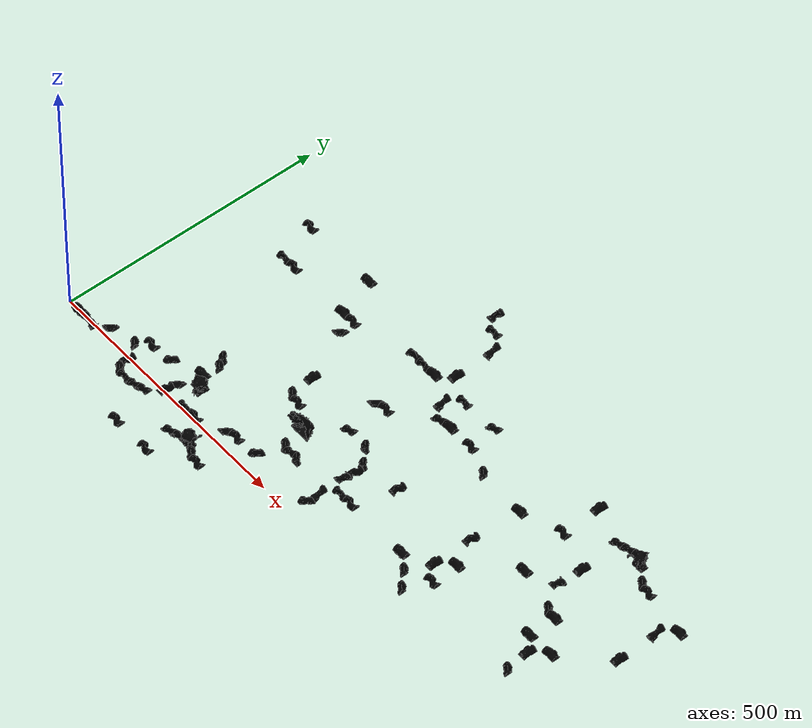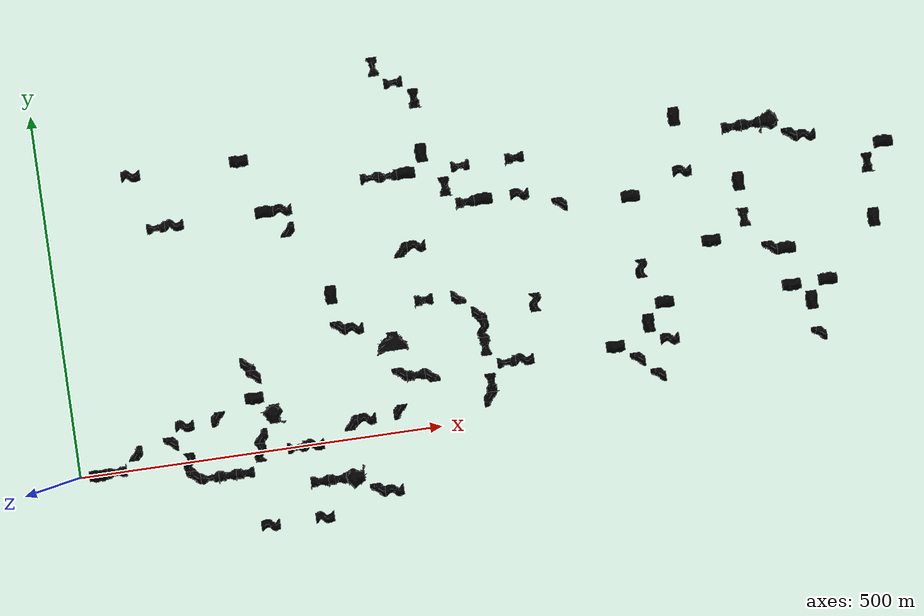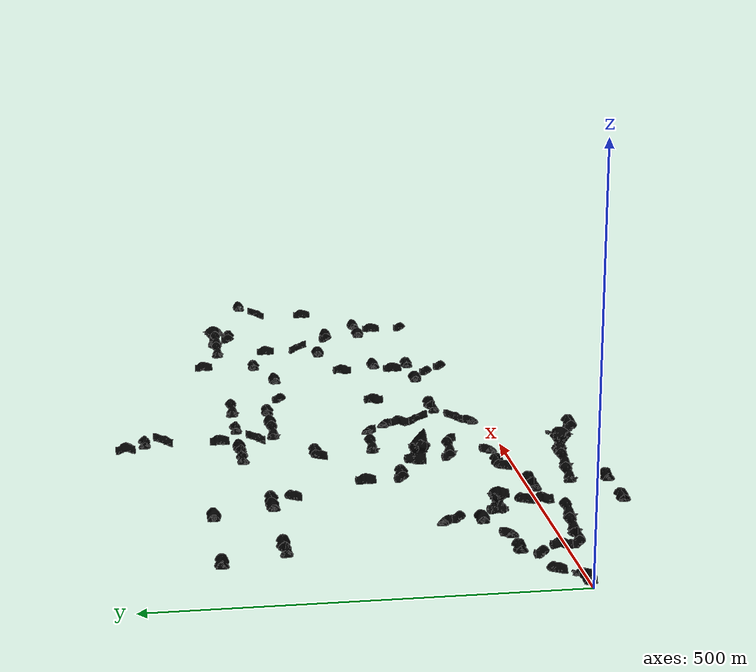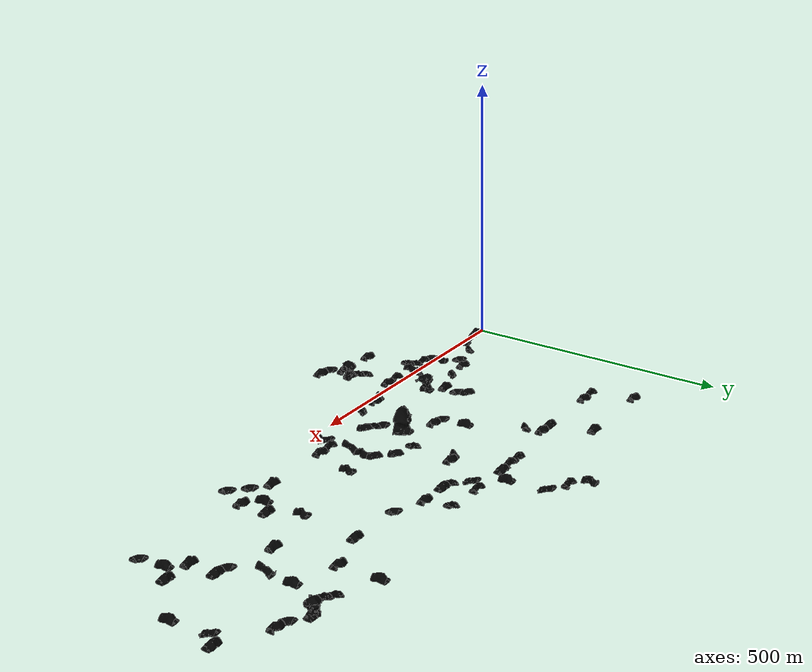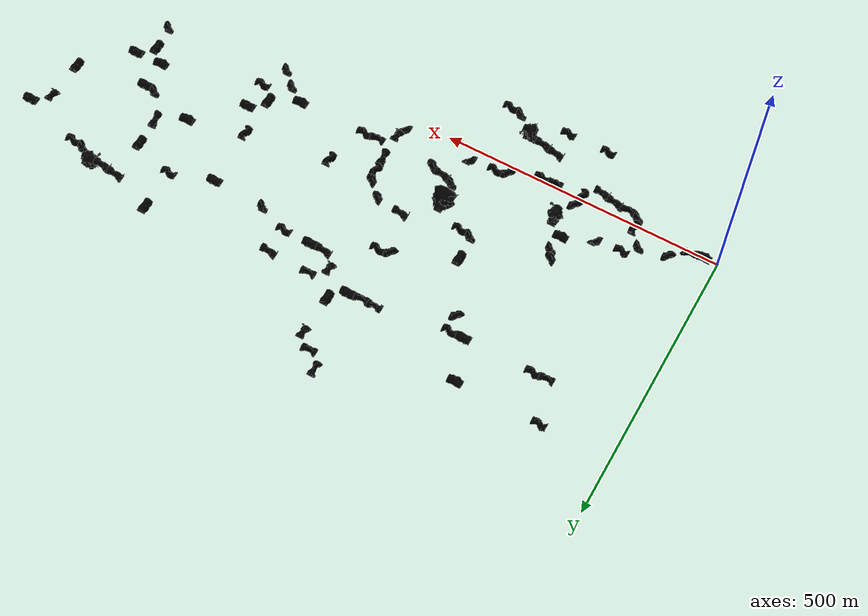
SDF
<sdf version="1.6">
 <world name="cave_circuit_practice_03">
  <physics name="1ms" type="ode">
   <max_step_size>0.004</max_step_size>
   <real_time_factor>1.0</real_time_factor>
  </physics>
  <scene>
   <ambient>0.1 0.1 0.1 1.0</ambient>
   <background>0 0 0 1.0</background>
   <grid>false</grid>
   <origin_visual>false</origin_visual>
  </scene>
  <atmosphere type="adiabatic">
   <temperature>288</temperature>
   <temperature_gradient>0.4</temperature_gradient>
  </atmosphere>
  <model name="performer_detector_rockfall_1">
   <static>true</static>
   <pose>348.293000 224.719000 5.290740 0.0 0.0 0.0</pose>
   <plugin filename="libignition-gazebo-performer-detector-system.so" name="ignition::gazebo::systems::PerformerDetector">
    <topic>/subt_performer_detector</topic>
    <geometry><box><size>16 25 15</size></box></geometry>
   </plugin>
   <plugin name="ignition::gazebo::systems::TriggeredPublisher" filename="libignition-gazebo-triggered-publisher-system.so">
    <input type="ignition.msgs.Pose" topic="/subt_performer_detector">
     <match field="header.data">{
            key: "frame_id"
            value: "performer_detector_rockfall_1"
            }</match>
     <match field="header.data">{
            key: "state"
            value: "1"
            }</match>
    </input>
    <output type="ignition.msgs.Empty" topic="/model/dynamic_rocks_1/breadcrumbs/Rock/deploy"/>
   </plugin>
  </model>
  <model name="performer_detector_rockfall_2">
   <static>true</static>
   <pose>847.566000 125.260000 24.790600 0.0 0.0 0.0</pose>
   <plugin filename="libignition-gazebo-performer-detector-system.so" name="ignition::gazebo::systems::PerformerDetector">
    <topic>/subt_performer_detector</topic>
    <geometry><box><size>16 25 15</size></box></geometry>
   </plugin>
   <plugin name="ignition::gazebo::systems::TriggeredPublisher" filename="libignition-gazebo-triggered-publisher-system.so">
    <input type="ignition.msgs.Pose" topic="/subt_performer_detector">
     <match field="header.data">{
            key: "frame_id"
            value: "performer_detector_rockfall_2"
            }</match>
     <match field="header.data">{
            key: "state"
            value: "1"
            }</match>
    </input>
    <output type="ignition.msgs.Empty" topic="/model/dynamic_rocks_2/breadcrumbs/Rock/deploy"/>
   </plugin>
  </model>
  <model name="performer_detector_rockfall_3">
   <static>true</static>
   <pose>153.975000 4.009890 -3.875 0.0 0.0 0.0</pose>
   <plugin filename="libignition-gazebo-performer-detector-system.so" name="ignition::gazebo::systems::PerformerDetector">
    <topic>/subt_performer_detector</topic>
    <geometry><box><size>25 16 15</size></box></geometry>
   </plugin>
   <plugin name="ignition::gazebo::systems::TriggeredPublisher" filename="libignition-gazebo-triggered-publisher-system.so">
    <input type="ignition.msgs.Pose" topic="/subt_performer_detector">
     <match field="header.data">{
            key: "frame_id"
            value: "performer_detector_rockfall_3"
            }</match>
     <match field="header.data">{
            key: "state"
            value: "0"
            }</match>
    </input>
    <output type="ignition.msgs.Empty" topic="/model/dynamic_rocks_3/breadcrumbs/Rock/deploy"/>
   </plugin>
  </model>
  <model name="performer_detector_rockfall_4">
   <static>true</static>
   <pose>626.056000 300.805000 12.145300 0.0 0.0 0.0</pose>
   <plugin filename="libignition-gazebo-performer-detector-system.so" name="ignition::gazebo::systems::PerformerDetector">
    <topic>/subt_performer_detector</topic>
    <geometry><box><size>25 16 15</size></box></geometry>
   </plugin>
   <plugin name="ignition::gazebo::systems::TriggeredPublisher" filename="libignition-gazebo-triggered-publisher-system.so">
    <input type="ignition.msgs.Pose" topic="/subt_performer_detector">
     <match field="header.data">{
            key: "frame_id"
            value: "performer_detector_rockfall_4"
            }</match>
     <match field="header.data">{
            key: "state"
            value: "0"
            }</match>
    </input>
    <output type="ignition.msgs.Empty" topic="/model/dynamic_rocks_4/breadcrumbs/Rock/deploy"/>
   </plugin>
  </model>
  <include>
   <static>true</static>
   <name>tile_3</name>
   <pose>75 25 -10 0 -0 3.14159</pose>
   <uri>https://fuel.ignitionrobotics.org/1.0/OpenRobotics/models/Cave Corner 02 Type B</uri>
  </include>
  <include>
   <static>true</static>
   <name>tile_4</name>
   <pose>50 0 -10 0 0 -1.5708</pose>
   <uri>https://fuel.ignitionrobotics.org/1.0/OpenRobotics/models/Cave Elevation Lights Type B</uri>
  </include>
  <include>
   <static>true</static>
   <name>tile_6</name>
   <pose>175 -25 -10 0 0 -1.5708</pose>
   <uri>https://fuel.ignitionrobotics.org/1.0/OpenRobotics/models/Cave Straight 02 Lights Type B</uri>
  </include>
  <include>
   <static>true</static>
   <name>tile_7</name>
   <pose>150 50 -10 0 0 -1.5708</pose>
   <uri>https://fuel.ignitionrobotics.org/1.0/OpenRobotics/models/Cave Straight 03 Type B</uri>
  </include>
  <include>
   <static>true</static>
   <name>tile_8</name>
   <pose>25 0 0 0 -0 1.5708</pose>
   <uri>https://fuel.ignitionrobotics.org/1.0/OpenRobotics/models/Cave Straight 04 Type B</uri>
  </include>
  <include>
   <static>true</static>
   <name>tile_10</name>
   <pose>275 50 -10 0 -0 3.14159</pose>
   <uri>https://fuel.ignitionrobotics.org/1.0/OpenRobotics/models/Cave Vertical Shaft Lights Type B</uri>
  </include>
  <include>
   <static>true</static>
   <name>tile_13</name>
   <pose>200 -25 -10 0 -0 1.5708</pose>
   <uri>https://fuel.ignitionrobotics.org/1.0/OpenRobotics/models/Cave Elevation Type B</uri>
  </include>
  <include>
   <static>true</static>
   <name>tile_15</name>
   <pose>200 50 -10 0 0 -0</pose>
   <uri>https://fuel.ignitionrobotics.org/1.0/OpenRobotics/models/Cave Corner 02 Lights Type B</uri>
  </include>
  <include>
   <static>true</static>
   <name>tile_16</name>
   <pose>125 25 -10 0 0 -1.5708</pose>
   <uri>https://fuel.ignitionrobotics.org/1.0/OpenRobotics/models/Cave Corner 02 Type B</uri>
  </include>
  <include>
   <static>true</static>
   <name>tile_18</name>
   <pose>150 0 -10 0 -0 0</pose>
   <uri>https://fuel.ignitionrobotics.org/1.0/OpenRobotics/models/Cave Straight 03 Type B</uri>
  </include>
  <include>
   <static>true</static>
   <name>tile_19</name>
   <pose>150 -25 -10 0 0 -1.5708</pose>
   <uri>https://fuel.ignitionrobotics.org/1.0/OpenRobotics/models/Cave Corner 02 Lights Type B</uri>
  </include>
  <include>
   <static>true</static>
   <name>tile_20</name>
   <pose>225 -25 0 0 -0 1.5708</pose>
   <uri>https://fuel.ignitionrobotics.org/1.0/OpenRobotics/models/Cave Elevation Lights Type B</uri>
  </include>
  <include>
   <static>true</static>
   <name>tile_23</name>
   <pose>250 0 10 0 -0 0</pose>
   <uri>https://fuel.ignitionrobotics.org/1.0/OpenRobotics/models/Cave Straight 03 Type B</uri>
  </include>
  <include>
   <static>true</static>
   <name>tile_24</name>
   <pose>250 25 10 0 -0 3.14159</pose>
   <uri>https://fuel.ignitionrobotics.org/1.0/OpenRobotics/models/Cave Corner 02 Lights Type B</uri>
  </include>
  <include>
   <static>true</static>
   <name>tile_32</name>
   <pose>325 -100 10 0 0 -1.5708</pose>
   <uri>https://fuel.ignitionrobotics.org/1.0/OpenRobotics/models/Cave Straight 03 Type B</uri>
  </include>
  <include>
   <static>true</static>
   <name>tile_33</name>
   <pose>250 -100 10 0 -0 1.5708</pose>
   <uri>https://fuel.ignitionrobotics.org/1.0/OpenRobotics/models/Cave Straight 03 Type B</uri>
  </include>
  <include>
   <static>true</static>
   <name>tile_34</name>
   <pose>325 -50 10 0 -0 1.5708</pose>
   <uri>https://fuel.ignitionrobotics.org/1.0/OpenRobotics/models/Cave Elevation Type B</uri>
  </include>
  <include>
   <static>true</static>
   <name>tile_35</name>
   <pose>350 -50 20 0 -0 1.5708</pose>
   <uri>https://fuel.ignitionrobotics.org/1.0/OpenRobotics/models/Cave Elevation Type B</uri>
  </include>
  <include>
   <static>true</static>
   <name>tile_37</name>
   <pose>300 0 10 0 0 -1.5708</pose>
   <uri>https://fuel.ignitionrobotics.org/1.0/OpenRobotics/models/Cave Straight 02 Lights Type B</uri>
  </include>
  <include>
   <static>true</static>
   <name>tile_38</name>
   <pose>325 0 10 0 0 -1.5708</pose>
   <uri>https://fuel.ignitionrobotics.org/1.0/OpenRobotics/models/Cave Straight 03 Type B</uri>
  </include>
  <include>
   <static>true</static>
   <name>tile_40</name>
   <pose>250 100 -10 0 0 -1.5708</pose>
   <uri>https://fuel.ignitionrobotics.org/1.0/OpenRobotics/models/Cave Corner 02 Lights Type B</uri>
  </include>
  <include>
   <static>true</static>
   <name>tile_41</name>
   <pose>250 125 -10 0 -0 1.5708</pose>
   <uri>https://fuel.ignitionrobotics.org/1.0/OpenRobotics/models/Cave Corner 02 Type B</uri>
  </include>
  <include>
   <static>true</static>
   <name>tile_43</name>
   <pose>375 -50 30 0 0 -1.5708</pose>
   <uri>https://fuel.ignitionrobotics.org/1.0/OpenRobotics/models/Cave Vertical Shaft Lights Type B</uri>
  </include>
  <include>
   <static>true</static>
   <name>tile_45</name>
   <pose>400 -75 50 0 0 -1.5708</pose>
   <uri>https://fuel.ignitionrobotics.org/1.0/OpenRobotics/models/Cave Corner 02 Type B</uri>
  </include>
  <include>
   <static>true</static>
   <name>tile_46</name>
   <pose>425 -75 50 0 -0 1.5708</pose>
   <uri>https://fuel.ignitionrobotics.org/1.0/OpenRobotics/models/Cave Straight 03 Type B</uri>
  </include>
  <include>
   <static>true</static>
   <name>tile_49</name>
   <pose>375 25 10 0 -0 3.14159</pose>
   <uri>https://fuel.ignitionrobotics.org/1.0/OpenRobotics/models/Cave Corner 02 Lights Type B</uri>
  </include>
  <include>
   <static>true</static>
   <name>tile_52</name>
   <pose>400 25 10 0 -0 1.5708</pose>
   <uri>https://fuel.ignitionrobotics.org/1.0/OpenRobotics/models/Cave Straight 03 Type B</uri>
  </include>
  <include>
   <static>true</static>
   <name>tile_53</name>
   <pose>450 25 10 0 0 -0</pose>
   <uri>https://fuel.ignitionrobotics.org/1.0/OpenRobotics/models/Cave Corner 02 Lights Type B</uri>
  </include>
  <include>
   <static>true</static>
   <name>tile_58</name>
   <pose>500 75 10 0 -0 1.57079</pose>
   <uri>https://fuel.ignitionrobotics.org/1.0/OpenRobotics/models/Cave Corner 02 Lights Type B</uri>
  </include>
  <include>
   <static>true</static>
   <name>tile_59</name>
   <pose>475 75 0 0 -0 1.5708</pose>
   <uri>https://fuel.ignitionrobotics.org/1.0/OpenRobotics/models/Cave Elevation Type B</uri>
  </include>
  <include>
   <static>true</static>
   <name>tile_63</name>
   <pose>450 75 0 0 0 -1.5708</pose>
   <uri>https://fuel.ignitionrobotics.org/1.0/OpenRobotics/models/Cave Corner 02 Lights Type B</uri>
  </include>
  <include>
   <static>true</static>
   <name>tile_65</name>
   <pose>450 125 0 0 0 -1.5708</pose>
   <uri>https://fuel.ignitionrobotics.org/1.0/OpenRobotics/models/Cave Cavern Split 02 Type B</uri>
  </include>
  <include>
   <static>true</static>
   <name>tile_68</name>
   <pose>400 150 0 0 -0 1.5708</pose>
   <uri>https://fuel.ignitionrobotics.org/1.0/OpenRobotics/models/Cave Straight 03 Type B</uri>
  </include>
  <include>
   <static>true</static>
   <name>tile_71</name>
   <pose>500 175 0 0 -0 1.5708</pose>
   <uri>https://fuel.ignitionrobotics.org/1.0/OpenRobotics/models/Cave Elevation Type B</uri>
  </include>
  <include>
   <static>true</static>
   <name>tile_74</name>
   <pose>575 25 10 0 -0 0</pose>
   <uri>https://fuel.ignitionrobotics.org/1.0/OpenRobotics/models/Cave Corner 02 Type B</uri>
  </include>
  <include>
   <static>true</static>
   <name>tile_75</name>
   <pose>550 175 10 0 -0 1.5708</pose>
   <uri>https://fuel.ignitionrobotics.org/1.0/OpenRobotics/models/Cave Corner 02 Type B</uri>
  </include>
  <include>
   <static>true</static>
   <name>tile_76</name>
   <pose>575 150 10 0 -0 1.5708</pose>
   <uri>https://fuel.ignitionrobotics.org/1.0/OpenRobotics/models/Cave Corner 02 Type B</uri>
  </include>
  <include>
   <static>true</static>
   <name>tile_78</name>
   <pose>575 125 10 0 0 -0</pose>
   <uri>https://fuel.ignitionrobotics.org/1.0/OpenRobotics/models/Cave Straight 03 Type B</uri>
  </include>
  <include>
   <static>true</static>
   <name>tile_79</name>
   <pose>575 100 10 0 0 -0</pose>
   <uri>https://fuel.ignitionrobotics.org/1.0/OpenRobotics/models/Cave Elevation Type B</uri>
  </include>
  <include>
   <static>true</static>
   <name>tile_80</name>
   <pose>575 50 10 0 -0 3.14159</pose>
   <uri>https://fuel.ignitionrobotics.org/1.0/OpenRobotics/models/Cave Elevation Type B</uri>
  </include>
  <include>
   <static>true</static>
   <name>tile_81</name>
   <pose>375 150 0 0 0 -1.5708</pose>
   <uri>https://fuel.ignitionrobotics.org/1.0/OpenRobotics/models/Cave Corner 02 Type B</uri>
  </include>
  <include>
   <static>true</static>
   <name>tile_88</name>
   <pose>475 250 0 0 -0 3.14159</pose>
   <uri>https://fuel.ignitionrobotics.org/1.0/OpenRobotics/models/Cave Corner 02 Type B</uri>
  </include>
  <include>
   <static>true</static>
   <name>tile_92</name>
   <pose>500 250 0 0 -0 1.5708</pose>
   <uri>https://fuel.ignitionrobotics.org/1.0/OpenRobotics/models/Cave Straight 03 Type B</uri>
  </include>
  <include>
   <static>true</static>
   <name>tile_97</name>
   <pose>325 300 0 0 -0 3.14159</pose>
   <uri>https://fuel.ignitionrobotics.org/1.0/OpenRobotics/models/Cave Corner 02 Type B</uri>
  </include>
  <include>
   <static>true</static>
   <name>tile_108</name>
   <pose>175 325 0 0 0 -1.5708</pose>
   <uri>https://fuel.ignitionrobotics.org/1.0/OpenRobotics/models/Cave Straight 03 Type B</uri>
  </include>
  <include>
   <static>true</static>
   <name>tile_118</name>
   <pose>125 400 0 0 0 -1.5708</pose>
   <uri>https://fuel.ignitionrobotics.org/1.0/OpenRobotics/models/Cave Straight 03 Type B</uri>
  </include>
  <include>
   <static>true</static>
   <name>tile_119</name>
   <pose>325 325 0 0 -0 1.5708</pose>
   <uri>https://fuel.ignitionrobotics.org/1.0/OpenRobotics/models/Cave Straight 03 Type B</uri>
  </include>
  <include>
   <static>true</static>
   <name>tile_120</name>
   <pose>275 400 0 0 -0 1.5708</pose>
   <uri>https://fuel.ignitionrobotics.org/1.0/OpenRobotics/models/Cave Straight 04 Type B</uri>
  </include>
  <include>
   <static>true</static>
   <name>tile_121</name>
   <pose>300 325 0 0 0 -1.5708</pose>
   <uri>https://fuel.ignitionrobotics.org/1.0/OpenRobotics/models/Cave Straight 04 Type B</uri>
  </include>
  <include>
   <static>true</static>
   <name>tile_122</name>
   <pose>150 325 0 0 0 -1.5708</pose>
   <uri>https://fuel.ignitionrobotics.org/1.0/OpenRobotics/models/Cave Straight 02 Type B</uri>
  </include>
  <include>
   <static>true</static>
   <name>tile_123</name>
   <pose>375 200 0 0 -0 0</pose>
   <uri>https://fuel.ignitionrobotics.org/1.0/OpenRobotics/models/Cave Straight 04 Type B</uri>
  </include>
  <include>
   <static>true</static>
   <name>tile_124</name>
   <pose>250 75 -10 0 -0 1.5708</pose>
   <uri>https://fuel.ignitionrobotics.org/1.0/OpenRobotics/models/Cave Straight 04 Lights Type B</uri>
  </include>
  <include>
   <static>true</static>
   <name>tile_127</name>
   <pose>550 325 0 0 -0 3.14159</pose>
   <uri>https://fuel.ignitionrobotics.org/1.0/OpenRobotics/models/Cave Elevation Type B</uri>
  </include>
  <include>
   <static>true</static>
   <name>tile_130</name>
   <pose>525 375 10 0 -0 0</pose>
   <uri>https://fuel.ignitionrobotics.org/1.0/OpenRobotics/models/Cave Straight 04 Type B</uri>
  </include>
  <include>
   <static>true</static>
   <name>tile_133</name>
   <pose>525 450 10 0 -0 3.14159</pose>
   <uri>https://fuel.ignitionrobotics.org/1.0/OpenRobotics/models/Cave Elevation Type B</uri>
  </include>
  <include>
   <static>true</static>
   <name>tile_134</name>
   <pose>500 350 10 0 0 -1.5708</pose>
   <uri>https://fuel.ignitionrobotics.org/1.0/OpenRobotics/models/Cave Straight 04 Type B</uri>
  </include>
  <include>
   <static>true</static>
   <name>tile_135</name>
   <pose>475 350 10 0 0 -1.5708</pose>
   <uri>https://fuel.ignitionrobotics.org/1.0/OpenRobotics/models/Cave Straight 02 Type B</uri>
  </include>
  <include>
   <static>true</static>
   <name>tile_136</name>
   <pose>450 350 10 0 -0 1.5708</pose>
   <uri>https://fuel.ignitionrobotics.org/1.0/OpenRobotics/models/Cave Straight 02 Type B</uri>
  </include>
  <include>
   <static>true</static>
   <name>tile_137</name>
   <pose>575 350 10 0 0 -1.5708</pose>
   <uri>https://fuel.ignitionrobotics.org/1.0/OpenRobotics/models/Cave Straight 02 Type B</uri>
  </include>
  <include>
   <static>true</static>
   <name>tile_142</name>
   <pose>575 300 0 0 -0 1.5708</pose>
   <uri>https://fuel.ignitionrobotics.org/1.0/OpenRobotics/models/Cave Elevation Type B</uri>
  </include>
  <include>
   <static>true</static>
   <name>tile_144</name>
   <pose>600 300 10 0 0 -1.5708</pose>
   <uri>https://fuel.ignitionrobotics.org/1.0/OpenRobotics/models/Cave Straight 04 Type B</uri>
  </include>
  <include>
   <static>true</static>
   <name>tile_145</name>
   <pose>650 300 10 0 -0 1.5708</pose>
   <uri>https://fuel.ignitionrobotics.org/1.0/OpenRobotics/models/Cave Straight 03 Type B</uri>
  </include>
  <include>
   <static>true</static>
   <name>tile_153</name>
   <pose>600 75 20 0 0 -1.5708</pose>
   <uri>https://fuel.ignitionrobotics.org/1.0/OpenRobotics/models/Cave Straight 02 Type B</uri>
  </include>
  <include>
   <static>true</static>
   <name>tile_154</name>
   <pose>625 75 20 0 0 -1.5708</pose>
   <uri>https://fuel.ignitionrobotics.org/1.0/OpenRobotics/models/Cave Straight 03 Type B</uri>
  </include>
  <include>
   <static>true</static>
   <name>tile_155</name>
   <pose>750 75 20 0 -0 1.5708</pose>
   <uri>https://fuel.ignitionrobotics.org/1.0/OpenRobotics/models/Cave Straight 04 Type B</uri>
  </include>
  <include>
   <static>true</static>
   <name>tile_160</name>
   <pose>775 50 20 0 0 -1.5708</pose>
   <uri>https://fuel.ignitionrobotics.org/1.0/OpenRobotics/models/Cave Corner 02 Type B</uri>
  </include>
  <include>
   <static>true</static>
   <name>tile_162</name>
   <pose>800 25 20 0 0 -1.5708</pose>
   <uri>https://fuel.ignitionrobotics.org/1.0/OpenRobotics/models/Cave Corner 02 Type B</uri>
  </include>
  <include>
   <static>true</static>
   <name>tile_167</name>
   <pose>825 75 20 0 -0 1.5708</pose>
   <uri>https://fuel.ignitionrobotics.org/1.0/OpenRobotics/models/Cave Straight 03 Type B</uri>
  </include>
  <include>
   <static>true</static>
   <name>tile_168</name>
   <pose>800 100 20 0 -0 0</pose>
   <uri>https://fuel.ignitionrobotics.org/1.0/OpenRobotics/models/Cave Straight 04 Type B</uri>
  </include>
  <include>
   <static>true</static>
   <name>tile_169</name>
   <pose>800 175 20 0 0 -3.14159</pose>
   <uri>https://fuel.ignitionrobotics.org/1.0/OpenRobotics/models/Cave Straight 03 Type B</uri>
  </include>
  <include>
   <static>true</static>
   <name>tile_174</name>
   <pose>900 200 20 0 -0 1.5708</pose>
   <uri>https://fuel.ignitionrobotics.org/1.0/OpenRobotics/models/Cave Straight 04 Type B</uri>
  </include>
  <include>
   <static>true</static>
   <name>tile_183</name>
   <pose>825 125 20 0 0 -1.5708</pose>
   <uri>https://fuel.ignitionrobotics.org/1.0/OpenRobotics/models/Cave Straight 04 Type B</uri>
  </include>
  <include>
   <static>true</static>
   <name>tile_188</name>
   <pose>1000 125 20 0 -0 1.5708</pose>
   <uri>https://fuel.ignitionrobotics.org/1.0/OpenRobotics/models/Cave Straight 04 Type B</uri>
  </include>
  <include>
   <static>true</static>
   <name>tile_190</name>
   <pose>975 175 20 0 0 -1.5708</pose>
   <uri>https://fuel.ignitionrobotics.org/1.0/OpenRobotics/models/Cave Corner 02 Type B</uri>
  </include>
  <include>
   <static>true</static>
   <name>tile_191</name>
   <pose>1000 175 20 0 0 -1.5708</pose>
   <uri>https://fuel.ignitionrobotics.org/1.0/OpenRobotics/models/Cave Straight 04 Type B</uri>
  </include>
  <include>
   <static>true</static>
   <name>tile_195</name>
   <pose>950 275 10 0 -0 0</pose>
   <uri>https://fuel.ignitionrobotics.org/1.0/OpenRobotics/models/Cave Straight 04 Type B</uri>
  </include>
  <include>
   <static>true</static>
   <name>tile_200</name>
   <pose>1025 325 10 0 0 -1.5708</pose>
   <uri>https://fuel.ignitionrobotics.org/1.0/OpenRobotics/models/Cave Corner 02 Type B</uri>
  </include>
  <include>
   <static>true</static>
   <name>tile_201</name>
   <pose>950 350 10 0 -0 1.5708</pose>
   <uri>https://fuel.ignitionrobotics.org/1.0/OpenRobotics/models/Cave Elevation Type B</uri>
  </include>
  <include>
   <static>true</static>
   <name>tile_202</name>
   <pose>975 350 20 0 -0 1.5708</pose>
   <uri>https://fuel.ignitionrobotics.org/1.0/OpenRobotics/models/Cave Elevation Type B</uri>
  </include>
  <include>
   <static>true</static>
   <name>tile_203</name>
   <pose>875 300 10 0 -0 1.5708</pose>
   <uri>https://fuel.ignitionrobotics.org/1.0/OpenRobotics/models/Cave Straight 03 Type B</uri>
  </include>
  <include>
   <static>true</static>
   <name>tile_204</name>
   <pose>1050 325 10 0 -0 1.5708</pose>
   <uri>https://fuel.ignitionrobotics.org/1.0/OpenRobotics/models/Cave Straight 03 Type B</uri>
  </include>
  <include>
   <static>true</static>
   <name>tile_208</name>
   <pose>1000 350 10 0 -0 1.5708</pose>
   <uri>https://fuel.ignitionrobotics.org/1.0/OpenRobotics/models/Cave Vertical Shaft Type B</uri>
  </include>
  <include>
   <static>true</static>
   <name>tile_211</name>
   <pose>700 275 10 0 0 -1.5708</pose>
   <uri>https://fuel.ignitionrobotics.org/1.0/OpenRobotics/models/Cave Corner 02 Type B</uri>
  </include>
  <include>
   <static>true</static>
   <name>tile_213</name>
   <pose>800 275 10 0 0 -1.5708</pose>
   <uri>https://fuel.ignitionrobotics.org/1.0/OpenRobotics/models/Cave Straight 04 Type B</uri>
  </include>
  <include>
   <static>true</static>
   <name>tile_220</name>
   <pose>875 375 10 0 -0 0</pose>
   <uri>https://fuel.ignitionrobotics.org/1.0/OpenRobotics/models/Cave Straight 04 Type B</uri>
  </include>
  <include>
   <static>true</static>
   <name>tile_223</name>
   <pose>1025 50 20 0 0 -1.5708</pose>
   <uri>https://fuel.ignitionrobotics.org/1.0/OpenRobotics/models/Cave Corner 02 Type B</uri>
  </include>
  <include>
   <static>true</static>
   <name>tile_225</name>
   <pose>1025 100 20 0 -0 0</pose>
   <uri>https://fuel.ignitionrobotics.org/1.0/OpenRobotics/models/Cave Straight 04 Type B</uri>
  </include>
  <include>
   <static>true</static>
   <name>tile_229</name>
   <pose>1050 125 20 0 0 -1.5708</pose>
   <uri>https://fuel.ignitionrobotics.org/1.0/OpenRobotics/models/Cave Straight 04 Type B</uri>
  </include>
  <include>
   <static>true</static>
   <name>tile_230</name>
   <pose>650 150 20 0 0 -3.14159</pose>
   <uri>https://fuel.ignitionrobotics.org/1.0/OpenRobotics/models/Cave Straight 03 Type B</uri>
  </include>
  <include>
   <static>true</static>
   <name>tile_234</name>
   <pose>1125 275 20 0 -0 3.14159</pose>
   <uri>https://fuel.ignitionrobotics.org/1.0/OpenRobotics/models/Cave Elevation Type B</uri>
  </include>
  <include>
   <static>true</static>
   <name>tile_236</name>
   <pose>1125 200 20 0 -0 0</pose>
   <uri>https://fuel.ignitionrobotics.org/1.0/OpenRobotics/models/Cave Straight 04 Type B</uri>
  </include>
  <include>
   <static>true</static>
   <name>tile_238</name>
   <pose>650 350 10 0 -0 1.5708</pose>
   <uri>https://fuel.ignitionrobotics.org/1.0/OpenRobotics/models/Cave Elevation Type B</uri>
  </include>
  <include>
   <static>true</static>
   <name>tile_239</name>
   <pose>500 475 20 0 0 -1.5708</pose>
   <uri>https://fuel.ignitionrobotics.org/1.0/OpenRobotics/models/Cave Straight 02 Type B</uri>
  </include>
  <include>
   <static>true</static>
   <name>tile_241</name>
   <pose>475 500 20 0 0 -0</pose>
   <uri>https://fuel.ignitionrobotics.org/1.0/OpenRobotics/models/Cave Straight 02 Type B</uri>
  </include>
  <include>
   <static>true</static>
   <name>tile_243</name>
   <pose>1150 300 30 0 0 -1.5708</pose>
   <uri>https://fuel.ignitionrobotics.org/1.0/OpenRobotics/models/Cave Straight 04 Type B</uri>
  </include>
  <include>
   <static>true</static>
   <name>tile_245</name>
   <pose>950 225 10 0 -0 0</pose>
   <uri>https://fuel.ignitionrobotics.org/1.0/OpenRobotics/models/Cave Elevation Type B</uri>
  </include>
  <plugin name="ignition::gazebo" filename="dummy">
   <level name="level0">
    <ref>tile_8</ref>
    <pose>25 212.5 20 0 0 0</pose>
    <geometry><box><size>93.75 725 160</size></box></geometry>
    <buffer>12.5</buffer>
   </level>
   <level name="level1">
    <ref>tile_4</ref>
    <pose>50 212.5 20 0 0 0</pose>
    <geometry><box><size>93.75 725 160</size></box></geometry>
    <buffer>12.5</buffer>
   </level>
   <level name="level2">
    <ref>tile_2</ref>
    <ref>tile_3</ref>
    <pose>75 212.5 20 0 0 0</pose>
    <geometry><box><size>93.75 725 160</size></box></geometry>
    <buffer>12.5</buffer>
   </level>
   <level name="level3">
    <ref>helmet_1</ref>
    <pose>76.7324 212.5 20 0 0 0</pose>
    <geometry><box><size>93.75 725 160</size></box></geometry>
    <buffer>12.5</buffer>
   </level>
   <level name="level4">
    <ref>tile_1</ref>
    <ref>cave_cap_1</ref>
    <ref>tile_11</ref>
    <ref>cave_cap_32</ref>
    <pose>100 212.5 20 0 0 0</pose>
    <geometry><box><size>93.75 725 160</size></box></geometry>
    <buffer>12.5</buffer>
   </level>
   <level name="level5">
    <ref>tile_12</ref>
    <ref>tile_16</ref>
    <ref>tile_118</ref>
    <ref>cave_cap_33</ref>
    <pose>125 212.5 20 0 0 0</pose>
    <geometry><box><size>93.75 725 160</size></box></geometry>
    <buffer>12.5</buffer>
   </level>
   <level name="level6">
    <ref>tile_7</ref>
    <ref>tile_17</ref>
    <ref>tile_18</ref>
    <ref>tile_19</ref>
    <ref>tile_117</ref>
    <ref>tile_122</ref>
    <pose>150 212.5 20 0 0 0</pose>
    <geometry><box><size>93.75 725 160</size></box></geometry>
    <buffer>12.5</buffer>
   </level>
   <level name="level7">
    <ref>tile_6</ref>
    <ref>tile_9</ref>
    <ref>tile_108</ref>
    <ref>tile_116</ref>
    <pose>175 212.5 20 0 0 0</pose>
    <geometry><box><size>93.75 725 160</size></box></geometry>
    <buffer>12.5</buffer>
   </level>
   <level name="level8">
    <ref>helmet_2</ref>
    <pose>183.567 212.5 20 0 0 0</pose>
    <geometry><box><size>93.75 725 160</size></box></geometry>
    <buffer>12.5</buffer>
   </level>
   <level name="level9">
    <ref>tile_13</ref>
    <ref>tile_14</ref>
    <ref>tile_15</ref>
    <ref>cave_cap_4</ref>
    <ref>tile_107</ref>
    <ref>tile_109</ref>
    <ref>tile_110</ref>
    <ref>tile_112</ref>
    <pose>200 212.5 20 0 0 0</pose>
    <geometry><box><size>93.75 725 160</size></box></geometry>
    <buffer>12.5</buffer>
   </level>
   <level name="level10">
    <ref>tile_5</ref>
    <ref>tile_20</ref>
    <ref>cave_cap_2</ref>
    <ref>tile_42</ref>
    <ref>tile_106</ref>
    <ref>tile_113</ref>
    <ref>tile_114</ref>
    <ref>tile_115</ref>
    <ref>cave_cap_31</ref>
    <pose>225 212.5 20 0 0 0</pose>
    <geometry><box><size>93.75 725 160</size></box></geometry>
    <buffer>12.5</buffer>
   </level>
   <level name="level11">
    <ref>tile_21</ref>
    <ref>tile_22</ref>
    <ref>tile_23</ref>
    <ref>tile_24</ref>
    <ref>tile_33</ref>
    <ref>tile_40</ref>
    <ref>tile_41</ref>
    <ref>tile_105</ref>
    <ref>tile_111</ref>
    <ref>tile_124</ref>
    <pose>250 212.5 20 0 0 0</pose>
    <geometry><box><size>93.75 725 160</size></box></geometry>
    <buffer>12.5</buffer>
   </level>
   <level name="level12">
    <ref>rescue_randy_1</ref>
    <pose>258.444 212.5 20 0 0 0</pose>
    <geometry><box><size>93.75 725 160</size></box></geometry>
    <buffer>12.5</buffer>
   </level>
   <level name="level13">
    <ref>tile_10</ref>
    <ref>tile_25</ref>
    <ref>tile_26</ref>
    <ref>tile_27</ref>
    <ref>tile_31</ref>
    <ref>tile_36</ref>
    <ref>tile_39</ref>
    <ref>tile_104</ref>
    <ref>tile_120</ref>
    <pose>275 212.5 20 0 0 0</pose>
    <geometry><box><size>93.75 725 160</size></box></geometry>
    <buffer>12.5</buffer>
   </level>
   <level name="level14">
    <ref>rope_1</ref>
    <pose>285.375 212.5 20 0 0 0</pose>
    <geometry><box><size>93.75 725 160</size></box></geometry>
    <buffer>12.5</buffer>
   </level>
   <level name="level15">
    <ref>tile_28</ref>
    <ref>tile_29</ref>
    <ref>tile_30</ref>
    <ref>tile_37</ref>
    <ref>tile_121</ref>
    <ref>cave_cap_35</ref>
    <ref>phone_1</ref>
    <pose>300 212.5 20 0 0 0</pose>
    <geometry><box><size>93.75 725 160</size></box></geometry>
    <buffer>12.5</buffer>
   </level>
   <level name="level16">
    <ref>tile_32</ref>
    <ref>tile_34</ref>
    <ref>tile_38</ref>
    <ref>tile_94</ref>
    <ref>tile_95</ref>
    <ref>tile_96</ref>
    <ref>tile_97</ref>
    <ref>tile_119</ref>
    <pose>325 212.5 20 0 0 0</pose>
    <geometry><box><size>93.75 725 160</size></box></geometry>
    <buffer>12.5</buffer>
   </level>
   <level name="level17">
    <ref>rope_3</ref>
    <pose>332.624 212.5 20 0 0 0</pose>
    <geometry><box><size>93.75 725 160</size></box></geometry>
    <buffer>12.5</buffer>
   </level>
   <level name="level18">
    <ref>cave_cap_3</ref>
    <ref>tile_35</ref>
    <ref>tile_47</ref>
    <ref>tile_93</ref>
    <ref>tile_100</ref>
    <ref>tile_103</ref>
    <pose>350 212.5 20 0 0 0</pose>
    <geometry><box><size>93.75 725 160</size></box></geometry>
    <buffer>12.5</buffer>
   </level>
   <level name="level19">
    <ref>tile_43</ref>
    <ref>tile_48</ref>
    <ref>tile_49</ref>
    <ref>tile_81</ref>
    <ref>tile_82</ref>
    <ref>tile_83</ref>
    <ref>tile_98</ref>
    <ref>tile_99</ref>
    <ref>tile_123</ref>
    <ref>cave_cap_25</ref>
    <pose>375 212.5 20 0 0 0</pose>
    <geometry><box><size>93.75 725 160</size></box></geometry>
    <buffer>12.5</buffer>
   </level>
   <level name="level20">
    <ref>rope_2</ref>
    <pose>385.756 212.5 20 0 0 0</pose>
    <geometry><box><size>93.75 725 160</size></box></geometry>
    <buffer>12.5</buffer>
   </level>
   <level name="level21">
    <ref>tile_44</ref>
    <ref>tile_45</ref>
    <ref>tile_50</ref>
    <ref>tile_52</ref>
    <ref>tile_68</ref>
    <ref>tile_84</ref>
    <ref>tile_101</ref>
    <pose>400 212.5 20 0 0 0</pose>
    <geometry><box><size>93.75 725 160</size></box></geometry>
    <buffer>12.5</buffer>
   </level>
   <level name="level22">
    <ref>backpack_1</ref>
    <pose>422.954 212.5 20 0 0 0</pose>
    <geometry><box><size>93.75 725 160</size></box></geometry>
    <buffer>12.5</buffer>
   </level>
   <level name="level23">
    <ref>cave_cap_5</ref>
    <ref>tile_46</ref>
    <ref>tile_51</ref>
    <ref>tile_54</ref>
    <ref>cave_cap_7</ref>
    <ref>tile_67</ref>
    <ref>tile_85</ref>
    <ref>tile_102</ref>
    <ref>cave_cap_24</ref>
    <pose>425 212.5 20 0 0 0</pose>
    <geometry><box><size>93.75 725 160</size></box></geometry>
    <buffer>12.5</buffer>
   </level>
   <level name="level24">
    <ref>cave_cap_6</ref>
    <ref>tile_53</ref>
    <ref>tile_55</ref>
    <ref>tile_63</ref>
    <ref>tile_64</ref>
    <ref>tile_65</ref>
    <ref>tile_66</ref>
    <ref>tile_86</ref>
    <ref>tile_89</ref>
    <ref>tile_90</ref>
    <ref>tile_136</ref>
    <pose>450 212.5 20 0 0 0</pose>
    <geometry><box><size>93.75 725 160</size></box></geometry>
    <buffer>12.5</buffer>
   </level>
   <level name="level25">
    <ref>tile_56</ref>
    <ref>tile_59</ref>
    <ref>tile_69</ref>
    <ref>tile_70</ref>
    <ref>tile_87</ref>
    <ref>tile_88</ref>
    <ref>tile_135</ref>
    <ref>tile_240</ref>
    <ref>tile_241</ref>
    <ref>cave_cap_26</ref>
    <pose>475 212.5 20 0 0 0</pose>
    <geometry><box><size>93.75 725 160</size></box></geometry>
    <buffer>12.5</buffer>
   </level>
   <level name="level26">
    <ref>rescue_randy_2</ref>
    <pose>483.978 212.5 20 0 0 0</pose>
    <geometry><box><size>93.75 725 160</size></box></geometry>
    <buffer>12.5</buffer>
   </level>
   <level name="level27">
    <ref>tile_72</ref>
    <ref>cave_cap_9</ref>
    <ref>cave_cap_10</ref>
    <pose>487.5 212.5 20 0 0 0</pose>
    <geometry><box><size>93.75 725 160</size></box></geometry>
    <buffer>12.5</buffer>
   </level>
   <level name="level28">
    <ref>rope_4</ref>
    <pose>493.647 212.5 20 0 0 0</pose>
    <geometry><box><size>93.75 725 160</size></box></geometry>
    <buffer>12.5</buffer>
   </level>
   <level name="level29">
    <ref>tile_57</ref>
    <ref>tile_58</ref>
    <ref>tile_60</ref>
    <ref>tile_71</ref>
    <ref>tile_92</ref>
    <ref>tile_134</ref>
    <ref>tile_239</ref>
    <pose>500 212.5 20 0 0 0</pose>
    <geometry><box><size>93.75 725 160</size></box></geometry>
    <buffer>12.5</buffer>
   </level>
   <level name="level30">
    <ref>tile_61</ref>
    <ref>tile_73</ref>
    <ref>tile_91</ref>
    <ref>tile_129</ref>
    <ref>tile_130</ref>
    <ref>tile_131</ref>
    <ref>tile_132</ref>
    <ref>tile_133</ref>
    <ref>tile_237</ref>
    <pose>525 212.5 20 0 0 0</pose>
    <geometry><box><size>93.75 725 160</size></box></geometry>
    <buffer>12.5</buffer>
   </level>
   <level name="level31">
    <ref>tile_62</ref>
    <ref>tile_75</ref>
    <ref>tile_77</ref>
    <ref>tile_125</ref>
    <ref>tile_126</ref>
    <ref>tile_127</ref>
    <ref>tile_128</ref>
    <ref>tile_143</ref>
    <ref>cave_cap_23</ref>
    <ref>cave_cap_36</ref>
    <pose>550 212.5 20 0 0 0</pose>
    <geometry><box><size>93.75 725 160</size></box></geometry>
    <buffer>12.5</buffer>
   </level>
   <level name="level32">
    <ref>phone_2</ref>
    <pose>553.095 212.5 20 0 0 0</pose>
    <geometry><box><size>93.75 725 160</size></box></geometry>
    <buffer>12.5</buffer>
   </level>
   <level name="level33">
    <ref>backpack_2</ref>
    <pose>570.734 212.5 20 0 0 0</pose>
    <geometry><box><size>93.75 725 160</size></box></geometry>
    <buffer>12.5</buffer>
   </level>
   <level name="level34">
    <ref>tile_74</ref>
    <ref>tile_76</ref>
    <ref>tile_78</ref>
    <ref>tile_79</ref>
    <ref>tile_80</ref>
    <ref>tile_137</ref>
    <ref>tile_142</ref>
    <ref>tile_146</ref>
    <ref>tile_149</ref>
    <pose>575 212.5 20 0 0 0</pose>
    <geometry><box><size>93.75 725 160</size></box></geometry>
    <buffer>12.5</buffer>
   </level>
   <level name="level35">
    <ref>tile_138</ref>
    <ref>tile_144</ref>
    <ref>tile_148</ref>
    <ref>tile_153</ref>
    <pose>600 212.5 20 0 0 0</pose>
    <geometry><box><size>93.75 725 160</size></box></geometry>
    <buffer>12.5</buffer>
   </level>
   <level name="level36">
    <ref>tile_139</ref>
    <ref>tile_140</ref>
    <ref>tile_141</ref>
    <ref>tile_154</ref>
    <ref>cave_cap_19</ref>
    <pose>625 212.5 20 0 0 0</pose>
    <geometry><box><size>93.75 725 160</size></box></geometry>
    <buffer>12.5</buffer>
   </level>
   <level name="level37">
    <ref>cave_cap_8</ref>
    <ref>tile_145</ref>
    <ref>tile_150</ref>
    <ref>tile_151</ref>
    <ref>tile_156</ref>
    <ref>tile_230</ref>
    <ref>tile_238</ref>
    <pose>650 212.5 20 0 0 0</pose>
    <geometry><box><size>93.75 725 160</size></box></geometry>
    <buffer>12.5</buffer>
   </level>
   <level name="level38">
    <ref>helmet_3</ref>
    <pose>656.799 212.5 20 0 0 0</pose>
    <geometry><box><size>93.75 725 160</size></box></geometry>
    <buffer>12.5</buffer>
   </level>
   <level name="level39">
    <ref>tile_147</ref>
    <ref>tile_158</ref>
    <ref>cave_cap_22</ref>
    <pose>675 212.5 20 0 0 0</pose>
    <geometry><box><size>93.75 725 160</size></box></geometry>
    <buffer>12.5</buffer>
   </level>
   <level name="level40">
    <ref>tile_157</ref>
    <ref>tile_210</ref>
    <ref>tile_211</ref>
    <pose>700 212.5 20 0 0 0</pose>
    <geometry><box><size>93.75 725 160</size></box></geometry>
    <buffer>12.5</buffer>
   </level>
   <level name="level41">
    <ref>tile_152</ref>
    <ref>tile_214</ref>
    <ref>cave_cap_16</ref>
    <ref>cave_cap_18</ref>
    <pose>725 212.5 20 0 0 0</pose>
    <geometry><box><size>93.75 725 160</size></box></geometry>
    <buffer>12.5</buffer>
   </level>
   <level name="level42">
    <ref>backpack_3</ref>
    <pose>738.731 212.5 20 0 0 0</pose>
    <geometry><box><size>93.75 725 160</size></box></geometry>
    <buffer>12.5</buffer>
   </level>
   <level name="level43">
    <ref>tile_155</ref>
    <ref>tile_171</ref>
    <ref>tile_215</ref>
    <pose>750 212.5 20 0 0 0</pose>
    <geometry><box><size>93.75 725 160</size></box></geometry>
    <buffer>12.5</buffer>
   </level>
   <level name="level44">
    <ref>helmet_4</ref>
    <pose>772.515 212.5 20 0 0 0</pose>
    <geometry><box><size>93.75 725 160</size></box></geometry>
    <buffer>12.5</buffer>
   </level>
   <level name="level45">
    <ref>tile_159</ref>
    <ref>tile_160</ref>
    <ref>tile_172</ref>
    <ref>tile_212</ref>
    <pose>775 212.5 20 0 0 0</pose>
    <geometry><box><size>93.75 725 160</size></box></geometry>
    <buffer>12.5</buffer>
   </level>
   <level name="level46">
    <ref>rescue_randy_3</ref>
    <pose>799.346 212.5 20 0 0 0</pose>
    <geometry><box><size>93.75 725 160</size></box></geometry>
    <buffer>12.5</buffer>
   </level>
   <level name="level47">
    <ref>tile_161</ref>
    <ref>tile_162</ref>
    <ref>tile_165</ref>
    <ref>tile_166</ref>
    <ref>tile_168</ref>
    <ref>tile_169</ref>
    <ref>tile_170</ref>
    <ref>tile_180</ref>
    <ref>tile_213</ref>
    <pose>800 212.5 20 0 0 0</pose>
    <geometry><box><size>93.75 725 160</size></box></geometry>
    <buffer>12.5</buffer>
   </level>
   <level name="level48">
    <ref>tile_163</ref>
    <ref>tile_167</ref>
    <ref>tile_183</ref>
    <ref>tile_218</ref>
    <ref>cave_cap_15</ref>
    <ref>tile_246</ref>
    <pose>825 212.5 20 0 0 0</pose>
    <geometry><box><size>93.75 725 160</size></box></geometry>
    <buffer>12.5</buffer>
   </level>
   <level name="level49">
    <ref>tile_164</ref>
    <ref>tile_175</ref>
    <ref>tile_182</ref>
    <ref>tile_216</ref>
    <ref>tile_217</ref>
    <ref>tile_219</ref>
    <ref>cave_cap_14</ref>
    <ref>cave_cap_27</ref>
    <pose>850 212.5 20 0 0 0</pose>
    <geometry><box><size>93.75 725 160</size></box></geometry>
    <buffer>12.5</buffer>
   </level>
   <level name="level50">
    <ref>tile_173</ref>
    <ref>tile_184</ref>
    <ref>tile_199</ref>
    <ref>tile_203</ref>
    <ref>tile_220</ref>
    <ref>cave_cap_17</ref>
    <ref>cave_cap_28</ref>
    <pose>875 212.5 20 0 0 0</pose>
    <geometry><box><size>93.75 725 160</size></box></geometry>
    <buffer>12.5</buffer>
   </level>
   <level name="level51">
    <ref>tile_174</ref>
    <ref>tile_185</ref>
    <ref>tile_205</ref>
    <ref>tile_206</ref>
    <pose>900 212.5 20 0 0 0</pose>
    <geometry><box><size>93.75 725 160</size></box></geometry>
    <buffer>12.5</buffer>
   </level>
   <level name="level52">
    <ref>tile_176</ref>
    <ref>tile_178</ref>
    <ref>tile_179</ref>
    <ref>tile_181</ref>
    <ref>tile_196</ref>
    <ref>tile_198</ref>
    <ref>tile_207</ref>
    <pose>925 212.5 20 0 0 0</pose>
    <geometry><box><size>93.75 725 160</size></box></geometry>
    <buffer>12.5</buffer>
   </level>
   <level name="level53">
    <ref>tile_177</ref>
    <ref>tile_186</ref>
    <ref>tile_194</ref>
    <ref>tile_195</ref>
    <ref>cave_cap_11</ref>
    <ref>tile_201</ref>
    <ref>tile_209</ref>
    <ref>tile_245</ref>
    <pose>950 212.5 20 0 0 0</pose>
    <geometry><box><size>93.75 725 160</size></box></geometry>
    <buffer>12.5</buffer>
   </level>
   <level name="level54">
    <ref>rescue_randy_4</ref>
    <pose>952.107 212.5 20 0 0 0</pose>
    <geometry><box><size>93.75 725 160</size></box></geometry>
    <buffer>12.5</buffer>
   </level>
   <level name="level55">
    <ref>tile_187</ref>
    <ref>tile_189</ref>
    <ref>tile_190</ref>
    <ref>tile_202</ref>
    <ref>cave_cap_34</ref>
    <pose>975 212.5 20 0 0 0</pose>
    <geometry><box><size>93.75 725 160</size></box></geometry>
    <buffer>12.5</buffer>
   </level>
   <level name="level56">
    <ref>tile_188</ref>
    <ref>tile_191</ref>
    <ref>tile_208</ref>
    <pose>1000 212.5 20 0 0 0</pose>
    <geometry><box><size>93.75 725 160</size></box></geometry>
    <buffer>12.5</buffer>
   </level>
   <level name="level57">
    <ref>rope_5</ref>
    <pose>1000.72 212.5 20 0 0 0</pose>
    <geometry><box><size>93.75 725 160</size></box></geometry>
    <buffer>12.5</buffer>
   </level>
   <level name="level58">
    <ref>tile_193</ref>
    <ref>tile_197</ref>
    <ref>tile_200</ref>
    <ref>tile_221</ref>
    <ref>tile_223</ref>
    <ref>tile_225</ref>
    <ref>tile_226</ref>
    <pose>1025 212.5 20 0 0 0</pose>
    <geometry><box><size>93.75 725 160</size></box></geometry>
    <buffer>12.5</buffer>
   </level>
   <level name="level59">
    <ref>tile_192</ref>
    <ref>cave_cap_12</ref>
    <ref>tile_204</ref>
    <ref>tile_229</ref>
    <ref>cave_cap_29</ref>
    <pose>1050 212.5 20 0 0 0</pose>
    <geometry><box><size>93.75 725 160</size></box></geometry>
    <buffer>12.5</buffer>
   </level>
   <level name="level60">
    <ref>cave_cap_13</ref>
    <ref>tile_222</ref>
    <ref>tile_227</ref>
    <ref>tile_228</ref>
    <pose>1075 212.5 20 0 0 0</pose>
    <geometry><box><size>93.75 725 160</size></box></geometry>
    <buffer>12.5</buffer>
   </level>
   <level name="level61">
    <ref>phone_3</ref>
    <pose>1081.91 212.5 20 0 0 0</pose>
    <geometry><box><size>93.75 725 160</size></box></geometry>
    <buffer>12.5</buffer>
   </level>
   <level name="level62">
    <ref>tile_224</ref>
    <ref>cave_cap_20</ref>
    <pose>1100 212.5 20 0 0 0</pose>
    <geometry><box><size>93.75 725 160</size></box></geometry>
    <buffer>12.5</buffer>
   </level>
   <level name="level63">
    <ref>tile_231</ref>
    <ref>tile_233</ref>
    <ref>tile_234</ref>
    <ref>tile_235</ref>
    <ref>tile_236</ref>
    <ref>tile_242</ref>
    <pose>1125 212.5 20 0 0 0</pose>
    <geometry><box><size>93.75 725 160</size></box></geometry>
    <buffer>12.5</buffer>
   </level>
   <level name="level64">
    <ref>backpack_4</ref>
    <pose>1131.69 212.5 20 0 0 0</pose>
    <geometry><box><size>93.75 725 160</size></box></geometry>
    <buffer>12.5</buffer>
   </level>
   <level name="level65">
    <ref>tile_232</ref>
    <ref>tile_243</ref>
    <pose>1150 212.5 20 0 0 0</pose>
    <geometry><box><size>93.75 725 160</size></box></geometry>
    <buffer>12.5</buffer>
   </level>
   <level name="level66">
    <ref>cave_cap_21</ref>
    <ref>tile_244</ref>
    <pose>1175 212.5 20 0 0 0</pose>
    <geometry><box><size>93.75 725 160</size></box></geometry>
    <buffer>12.5</buffer>
   </level>
   <level name="level67">
    <ref>cave_cap_30</ref>
    <pose>1200 212.5 20 0 0 0</pose>
    <geometry><box><size>93.75 725 160</size></box></geometry>
    <buffer>12.5</buffer>
   </level>
   <level name="level68">
    <ref>tile_30</ref>
    <ref>tile_31</ref>
    <ref>tile_32</ref>
    <ref>tile_33</ref>
    <ref>cave_cap_2</ref>
    <ref>cave_cap_3</ref>
    <pose>612.5 -100 20 0 0 0</pose>
    <geometry><box><size>1275 93.75 160</size></box></geometry>
    <buffer>12.5</buffer>
   </level>
   <level name="level69">
    <ref>phone_1</ref>
    <pose>612.5 -98.4731 20 0 0 0</pose>
    <geometry><box><size>1275 93.75 160</size></box></geometry>
    <buffer>12.5</buffer>
   </level>
   <level name="level70">
    <ref>tile_29</ref>
    <ref>tile_45</ref>
    <ref>tile_46</ref>
    <ref>cave_cap_6</ref>
    <pose>612.5 -75 20 0 0 0</pose>
    <geometry><box><size>1275 93.75 160</size></box></geometry>
    <buffer>12.5</buffer>
   </level>
   <level name="level71">
    <ref>rope_2</ref>
    <pose>612.5 -50.2785 20 0 0 0</pose>
    <geometry><box><size>1275 93.75 160</size></box></geometry>
    <buffer>12.5</buffer>
   </level>
   <level name="level72">
    <ref>tile_22</ref>
    <ref>tile_27</ref>
    <ref>tile_28</ref>
    <ref>tile_34</ref>
    <ref>tile_35</ref>
    <ref>tile_43</ref>
    <ref>tile_44</ref>
    <ref>cave_cap_5</ref>
    <pose>612.5 -50 20 0 0 0</pose>
    <geometry><box><size>1275 93.75 160</size></box></geometry>
    <buffer>12.5</buffer>
   </level>
   <level name="level73">
    <ref>tile_6</ref>
    <ref>tile_13</ref>
    <ref>tile_19</ref>
    <ref>tile_20</ref>
    <ref>tile_21</ref>
    <ref>cave_cap_7</ref>
    <pose>612.5 -25 20 0 0 0</pose>
    <geometry><box><size>1275 93.75 160</size></box></geometry>
    <buffer>12.5</buffer>
   </level>
   <level name="level74">
    <ref>backpack_1</ref>
    <pose>612.5 -2.32283 20 0 0 0</pose>
    <geometry><box><size>1275 93.75 160</size></box></geometry>
    <buffer>12.5</buffer>
   </level>
   <level name="level75">
    <ref>tile_2</ref>
    <ref>tile_4</ref>
    <ref>tile_8</ref>
    <ref>cave_cap_1</ref>
    <ref>tile_18</ref>
    <ref>tile_23</ref>
    <ref>tile_36</ref>
    <ref>tile_37</ref>
    <ref>tile_38</ref>
    <ref>tile_47</ref>
    <ref>tile_48</ref>
    <ref>tile_50</ref>
    <ref>tile_54</ref>
    <pose>612.5 0 20 0 0 0</pose>
    <geometry><box><size>1275 93.75 160</size></box></geometry>
    <buffer>12.5</buffer>
   </level>
   <level name="level76">
    <ref>helmet_1</ref>
    <pose>612.5 22.5743 20 0 0 0</pose>
    <geometry><box><size>1275 93.75 160</size></box></geometry>
    <buffer>12.5</buffer>
   </level>
   <level name="level77">
    <ref>tile_1</ref>
    <ref>tile_3</ref>
    <ref>tile_16</ref>
    <ref>tile_17</ref>
    <ref>tile_24</ref>
    <ref>tile_25</ref>
    <ref>tile_49</ref>
    <ref>tile_51</ref>
    <ref>tile_52</ref>
    <ref>tile_53</ref>
    <ref>tile_60</ref>
    <ref>tile_61</ref>
    <ref>tile_62</ref>
    <ref>tile_74</ref>
    <ref>tile_162</ref>
    <ref>tile_163</ref>
    <ref>tile_164</ref>
    <ref>cave_cap_28</ref>
    <pose>612.5 25 20 0 0 0</pose>
    <geometry><box><size>1275 93.75 160</size></box></geometry>
    <buffer>12.5</buffer>
   </level>
   <level name="level78">
    <ref>rescue_randy_3</ref>
    <pose>612.5 32.4765 20 0 0 0</pose>
    <geometry><box><size>1275 93.75 160</size></box></geometry>
    <buffer>12.5</buffer>
   </level>
   <level name="level79">
    <ref>tile_7</ref>
    <ref>tile_9</ref>
    <ref>tile_10</ref>
    <ref>tile_11</ref>
    <ref>tile_12</ref>
    <ref>tile_15</ref>
    <ref>tile_55</ref>
    <ref>tile_56</ref>
    <ref>tile_57</ref>
    <ref>tile_80</ref>
    <ref>tile_160</ref>
    <ref>tile_161</ref>
    <ref>tile_223</ref>
    <ref>cave_cap_29</ref>
    <pose>612.5 50 20 0 0 0</pose>
    <geometry><box><size>1275 93.75 160</size></box></geometry>
    <buffer>12.5</buffer>
   </level>
   <level name="level80">
    <ref>tile_5</ref>
    <ref>tile_14</ref>
    <ref>tile_26</ref>
    <ref>tile_58</ref>
    <ref>tile_59</ref>
    <ref>tile_63</ref>
    <ref>cave_cap_9</ref>
    <ref>tile_124</ref>
    <ref>tile_149</ref>
    <ref>tile_150</ref>
    <ref>tile_152</ref>
    <ref>tile_153</ref>
    <ref>tile_154</ref>
    <ref>tile_155</ref>
    <ref>tile_157</ref>
    <ref>tile_158</ref>
    <ref>tile_159</ref>
    <ref>tile_165</ref>
    <ref>tile_167</ref>
    <ref>tile_226</ref>
    <ref>cave_cap_27</ref>
    <pose>612.5 75 20 0 0 0</pose>
    <geometry><box><size>1275 93.75 160</size></box></geometry>
    <buffer>12.5</buffer>
   </level>
   <level name="level81">
    <ref>rope_1</ref>
    <pose>612.5 75.9282 20 0 0 0</pose>
    <geometry><box><size>1275 93.75 160</size></box></geometry>
    <buffer>12.5</buffer>
   </level>
   <level name="level82">
    <ref>tile_39</ref>
    <ref>tile_40</ref>
    <ref>tile_64</ref>
    <ref>tile_72</ref>
    <ref>tile_79</ref>
    <ref>tile_156</ref>
    <ref>tile_168</ref>
    <ref>tile_225</ref>
    <pose>612.5 100 20 0 0 0</pose>
    <geometry><box><size>1275 93.75 160</size></box></geometry>
    <buffer>12.5</buffer>
   </level>
   <level name="level83">
    <ref>rescue_randy_2</ref>
    <pose>612.5 111.766 20 0 0 0</pose>
    <geometry><box><size>1275 93.75 160</size></box></geometry>
    <buffer>12.5</buffer>
   </level>
   <level name="level84">
    <ref>phone_3</ref>
    <pose>612.5 120.843 20 0 0 0</pose>
    <geometry><box><size>1275 93.75 160</size></box></geometry>
    <buffer>12.5</buffer>
   </level>
   <level name="level85">
    <ref>tile_41</ref>
    <ref>tile_42</ref>
    <ref>cave_cap_4</ref>
    <ref>tile_65</ref>
    <ref>cave_cap_10</ref>
    <ref>tile_78</ref>
    <ref>tile_151</ref>
    <ref>tile_180</ref>
    <ref>tile_181</ref>
    <ref>tile_182</ref>
    <ref>tile_183</ref>
    <ref>tile_184</ref>
    <ref>tile_185</ref>
    <ref>tile_186</ref>
    <ref>tile_187</ref>
    <ref>tile_188</ref>
    <ref>tile_221</ref>
    <ref>tile_228</ref>
    <ref>tile_229</ref>
    <ref>cave_cap_20</ref>
    <pose>612.5 125 20 0 0 0</pose>
    <geometry><box><size>1275 93.75 160</size></box></geometry>
    <buffer>12.5</buffer>
   </level>
   <level name="level86">
    <ref>helmet_3</ref>
    <pose>612.5 130.784 20 0 0 0</pose>
    <geometry><box><size>1275 93.75 160</size></box></geometry>
    <buffer>12.5</buffer>
   </level>
   <level name="level87">
    <ref>backpack_2</ref>
    <pose>612.5 144.756 20 0 0 0</pose>
    <geometry><box><size>1275 93.75 160</size></box></geometry>
    <buffer>12.5</buffer>
   </level>
   <level name="level88">
    <ref>tile_66</ref>
    <ref>tile_67</ref>
    <ref>tile_68</ref>
    <ref>tile_69</ref>
    <ref>tile_76</ref>
    <ref>tile_77</ref>
    <ref>tile_81</ref>
    <ref>tile_166</ref>
    <ref>tile_178</ref>
    <ref>cave_cap_11</ref>
    <ref>tile_227</ref>
    <ref>tile_230</ref>
    <pose>612.5 150 20 0 0 0</pose>
    <geometry><box><size>1275 93.75 160</size></box></geometry>
    <buffer>12.5</buffer>
   </level>
   <level name="level89">
    <ref>tile_70</ref>
    <ref>cave_cap_8</ref>
    <ref>tile_71</ref>
    <ref>tile_73</ref>
    <ref>tile_75</ref>
    <ref>tile_82</ref>
    <ref>tile_169</ref>
    <ref>tile_179</ref>
    <ref>tile_190</ref>
    <ref>tile_191</ref>
    <ref>tile_192</ref>
    <ref>tile_193</ref>
    <ref>tile_222</ref>
    <ref>tile_224</ref>
    <ref>tile_231</ref>
    <ref>tile_232</ref>
    <ref>cave_cap_21</ref>
    <pose>612.5 175 20 0 0 0</pose>
    <geometry><box><size>1275 93.75 160</size></box></geometry>
    <buffer>12.5</buffer>
   </level>
   <level name="level90">
    <ref>backpack_3</ref>
    <pose>612.5 195.563 20 0 0 0</pose>
    <geometry><box><size>1275 93.75 160</size></box></geometry>
    <buffer>12.5</buffer>
   </level>
   <level name="level91">
    <ref>tile_123</ref>
    <ref>tile_170</ref>
    <ref>tile_171</ref>
    <ref>tile_172</ref>
    <ref>tile_173</ref>
    <ref>tile_174</ref>
    <ref>tile_175</ref>
    <ref>tile_176</ref>
    <ref>tile_177</ref>
    <ref>tile_189</ref>
    <ref>cave_cap_18</ref>
    <ref>tile_236</ref>
    <ref>tile_246</ref>
    <pose>612.5 200 20 0 0 0</pose>
    <geometry><box><size>1275 93.75 160</size></box></geometry>
    <buffer>12.5</buffer>
   </level>
   <level name="level92">
    <ref>rescue_randy_4</ref>
    <pose>612.5 207.951 20 0 0 0</pose>
    <geometry><box><size>1275 93.75 160</size></box></geometry>
    <buffer>12.5</buffer>
   </level>
   <level name="level93">
    <ref>tile_83</ref>
    <ref>tile_84</ref>
    <ref>tile_85</ref>
    <ref>tile_86</ref>
    <ref>tile_87</ref>
    <ref>tile_93</ref>
    <ref>tile_94</ref>
    <ref>cave_cap_14</ref>
    <ref>tile_235</ref>
    <ref>tile_245</ref>
    <pose>612.5 225 20 0 0 0</pose>
    <geometry><box><size>1275 93.75 160</size></box></geometry>
    <buffer>12.5</buffer>
   </level>
   <level name="level94">
    <ref>tile_88</ref>
    <ref>tile_89</ref>
    <ref>tile_91</ref>
    <ref>tile_92</ref>
    <ref>tile_95</ref>
    <ref>tile_125</ref>
    <ref>tile_146</ref>
    <ref>tile_148</ref>
    <ref>tile_194</ref>
    <ref>tile_219</ref>
    <ref>cave_cap_19</ref>
    <ref>tile_233</ref>
    <pose>612.5 250 20 0 0 0</pose>
    <geometry><box><size>1275 93.75 160</size></box></geometry>
    <buffer>12.5</buffer>
   </level>
   <level name="level95">
    <ref>backpack_4</ref>
    <pose>612.5 253.501 20 0 0 0</pose>
    <geometry><box><size>1275 93.75 160</size></box></geometry>
    <buffer>12.5</buffer>
   </level>
   <level name="level96">
    <ref>tile_90</ref>
    <ref>tile_96</ref>
    <ref>tile_99</ref>
    <ref>tile_101</ref>
    <ref>tile_102</ref>
    <ref>tile_126</ref>
    <ref>tile_195</ref>
    <ref>tile_211</ref>
    <ref>tile_212</ref>
    <ref>tile_213</ref>
    <ref>tile_214</ref>
    <ref>tile_215</ref>
    <ref>tile_217</ref>
    <ref>tile_218</ref>
    <ref>tile_234</ref>
    <pose>612.5 275 20 0 0 0</pose>
    <geometry><box><size>1275 93.75 160</size></box></geometry>
    <buffer>12.5</buffer>
   </level>
   <level name="level97">
    <ref>helmet_4</ref>
    <pose>612.5 279.329 20 0 0 0</pose>
    <geometry><box><size>1275 93.75 160</size></box></geometry>
    <buffer>12.5</buffer>
   </level>
   <level name="level98">
    <ref>rope_3</ref>
    <pose>612.5 292.106 20 0 0 0</pose>
    <geometry><box><size>1275 93.75 160</size></box></geometry>
    <buffer>12.5</buffer>
   </level>
   <level name="level99">
    <ref>tile_97</ref>
    <ref>tile_98</ref>
    <ref>tile_100</ref>
    <ref>tile_140</ref>
    <ref>tile_142</ref>
    <ref>tile_143</ref>
    <ref>tile_144</ref>
    <ref>tile_145</ref>
    <ref>tile_147</ref>
    <ref>tile_196</ref>
    <ref>tile_203</ref>
    <ref>tile_206</ref>
    <ref>tile_209</ref>
    <ref>tile_210</ref>
    <ref>tile_216</ref>
    <ref>cave_cap_15</ref>
    <ref>cave_cap_16</ref>
    <ref>tile_242</ref>
    <ref>tile_243</ref>
    <ref>cave_cap_30</ref>
    <ref>tile_244</ref>
    <ref>cave_cap_34</ref>
    <pose>612.5 300 20 0 0 0</pose>
    <geometry><box><size>1275 93.75 160</size></box></geometry>
    <buffer>12.5</buffer>
   </level>
   <level name="level100">
    <ref>helmet_2</ref>
    <pose>612.5 321.704 20 0 0 0</pose>
    <geometry><box><size>1275 93.75 160</size></box></geometry>
    <buffer>12.5</buffer>
   </level>
   <level name="level101">
    <ref>phone_2</ref>
    <pose>612.5 322.572 20 0 0 0</pose>
    <geometry><box><size>1275 93.75 160</size></box></geometry>
    <buffer>12.5</buffer>
   </level>
   <level name="level102">
    <ref>tile_103</ref>
    <ref>tile_104</ref>
    <ref>tile_105</ref>
    <ref>tile_106</ref>
    <ref>tile_107</ref>
    <ref>tile_108</ref>
    <ref>tile_119</ref>
    <ref>tile_121</ref>
    <ref>tile_122</ref>
    <ref>tile_127</ref>
    <ref>tile_141</ref>
    <ref>cave_cap_13</ref>
    <ref>tile_200</ref>
    <ref>tile_204</ref>
    <ref>tile_207</ref>
    <ref>cave_cap_25</ref>
    <ref>cave_cap_33</ref>
    <pose>612.5 325 20 0 0 0</pose>
    <geometry><box><size>1275 93.75 160</size></box></geometry>
    <buffer>12.5</buffer>
   </level>
   <level name="level103">
    <ref>rope_5</ref>
    <pose>612.5 346.636 20 0 0 0</pose>
    <geometry><box><size>1275 93.75 160</size></box></geometry>
    <buffer>12.5</buffer>
   </level>
   <level name="level104">
    <ref>tile_109</ref>
    <ref>tile_128</ref>
    <ref>tile_129</ref>
    <ref>tile_134</ref>
    <ref>tile_135</ref>
    <ref>tile_136</ref>
    <ref>tile_137</ref>
    <ref>tile_138</ref>
    <ref>tile_139</ref>
    <ref>tile_197</ref>
    <ref>tile_198</ref>
    <ref>cave_cap_12</ref>
    <ref>tile_199</ref>
    <ref>tile_201</ref>
    <ref>tile_202</ref>
    <ref>tile_205</ref>
    <ref>tile_208</ref>
    <ref>tile_238</ref>
    <ref>cave_cap_22</ref>
    <ref>cave_cap_24</ref>
    <pose>612.5 350 20 0 0 0</pose>
    <geometry><box><size>1275 93.75 160</size></box></geometry>
    <buffer>12.5</buffer>
   </level>
   <level name="level105">
    <ref>tile_110</ref>
    <ref>tile_130</ref>
    <ref>tile_220</ref>
    <pose>612.5 375 20 0 0 0</pose>
    <geometry><box><size>1275 93.75 160</size></box></geometry>
    <buffer>12.5</buffer>
   </level>
   <level name="level106">
    <ref>rescue_randy_1</ref>
    <pose>612.5 394.08 20 0 0 0</pose>
    <geometry><box><size>1275 93.75 160</size></box></geometry>
    <buffer>12.5</buffer>
   </level>
   <level name="level107">
    <ref>tile_111</ref>
    <ref>tile_112</ref>
    <ref>tile_113</ref>
    <ref>tile_116</ref>
    <ref>tile_117</ref>
    <ref>tile_118</ref>
    <ref>tile_120</ref>
    <ref>tile_131</ref>
    <ref>cave_cap_17</ref>
    <ref>cave_cap_32</ref>
    <ref>cave_cap_35</ref>
    <pose>612.5 400 20 0 0 0</pose>
    <geometry><box><size>1275 93.75 160</size></box></geometry>
    <buffer>12.5</buffer>
   </level>
   <level name="level108">
    <ref>tile_114</ref>
    <ref>tile_132</ref>
    <ref>cave_cap_36</ref>
    <pose>612.5 425 20 0 0 0</pose>
    <geometry><box><size>1275 93.75 160</size></box></geometry>
    <buffer>12.5</buffer>
   </level>
   <level name="level109">
    <ref>tile_115</ref>
    <ref>tile_133</ref>
    <pose>612.5 450 20 0 0 0</pose>
    <geometry><box><size>1275 93.75 160</size></box></geometry>
    <buffer>12.5</buffer>
   </level>
   <level name="level110">
    <ref>tile_237</ref>
    <ref>cave_cap_23</ref>
    <ref>tile_239</ref>
    <ref>tile_240</ref>
    <ref>cave_cap_31</ref>
    <pose>612.5 475 20 0 0 0</pose>
    <geometry><box><size>1275 93.75 160</size></box></geometry>
    <buffer>12.5</buffer>
   </level>
   <level name="level111">
    <ref>rope_4</ref>
    <pose>612.5 478.193 20 0 0 0</pose>
    <geometry><box><size>1275 93.75 160</size></box></geometry>
    <buffer>12.5</buffer>
   </level>
   <level name="level112">
    <ref>tile_241</ref>
    <pose>612.5 500 20 0 0 0</pose>
    <geometry><box><size>1275 93.75 160</size></box></geometry>
    <buffer>12.5</buffer>
   </level>
   <level name="level113">
    <ref>cave_cap_26</ref>
    <pose>612.5 525 20 0 0 0</pose>
    <geometry><box><size>1275 93.75 160</size></box></geometry>
    <buffer>12.5</buffer>
   </level>
  </plugin>
 </world>
</sdf>

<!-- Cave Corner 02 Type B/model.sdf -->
<sdf version="1.6">
  <model name="Cave Corner 02 Type B">
    <static>true</static>
    <link name="base_link">
      <collision name="collision">
        <pose>0 0 0 0 0 0</pose>
        <geometry>
          <mesh>
            <uri>model://cave_corner_02/meshes/cavecorner02.dae</uri>
            <scale>1.005 1.005 1.0</scale>
          </mesh>
        </geometry>
      </collision>
      <visual name="CaveWall_visual">
        <geometry>
          <mesh>
            <uri>model://cave_corner_02/meshes/cavecorner02.dae</uri>
            <submesh>
              <name>CaveWall</name>
              <center>false</center>
            </submesh>
            <scale>1.005 1.005 1.0</scale>
          </mesh>
        </geometry>
        <material>
          <diffuse>0 0 0 1</diffuse>
          <specular>0 0 0 1</specular>
          <pbr>
            <metal>
              <albedo_map>model://cave_corner_02/materials/textures/CaveWall_Albedo.png</albedo_map>
              <normal_map>model://cave_corner_02/materials/textures/CaveWall_Normal.png</normal_map>
              <roughness_map>model://cave_corner_02/materials/textures/CaveWall_Roughness.png</roughness_map>
            </metal>
          </pbr>

          <script>
            <uri>model://cave_corner_02/materials/scripts/</uri>
            <uri>model://cave_corner_02/materials/textures/</uri>
            <name>CaveTile/CaveWall_Diffuse</name>
          </script>
        </material>
      </visual>
      <visual name="StriatedRock_visual">
        <geometry>
          <mesh>
            <uri>model://cave_corner_02/meshes/cavecorner02.dae</uri>
            <submesh>
              <name>StriatedRock</name>
              <center>false</center>
            </submesh>
            <scale>1.005 1.005 1.0</scale>
          </mesh>
        </geometry>
        <material>
          <diffuse>0 0 0 1</diffuse>
          <specular>0 0 0 1</specular>
          <pbr>
            <metal>
              <albedo_map>model://cave_corner_02/materials/textures/StriatedRock_Albedo.png</albedo_map>
              <normal_map>model://cave_corner_02/materials/textures/StriatedRock_Normal.png</normal_map>
              <roughness_map>model://cave_corner_02/materials/textures/StriatedRock_Roughness.png</roughness_map>
            </metal>
          </pbr>

          <script>
            <uri>model://cave_corner_02/materials/scripts/</uri>
            <uri>model://cave_corner_02/materials/textures/</uri>
            <name>CaveTile/StriatedRock_Diffuse</name>
          </script>
        </material>
      </visual>
      <visual name="RockPile_visual">
        <geometry>
          <mesh>
            <uri>model://cave_corner_02/meshes/cavecorner02.dae</uri>
            <submesh>
              <name>RockPile</name>
              <center>false</center>
            </submesh>
            <scale>1.005 1.005 1.0</scale>
          </mesh>
        </geometry>
        <material>
          <diffuse>0 0 0 1</diffuse>
          <specular>0 0 0 1</specular>
          <pbr>
            <metal>
              <albedo_map>model://cave_corner_02/materials/textures/RockPile_Albedo.png</albedo_map>
              <normal_map>model://cave_corner_02/materials/textures/RockPile_Normal.png</normal_map>
              <roughness_map>model://cave_corner_02/materials/textures/RockPile_Roughness.png</roughness_map>
            </metal>
          </pbr>

          <script>
            <uri>model://cave_corner_02/materials/scripts/</uri>
            <uri>model://cave_corner_02/materials/textures/</uri>
            <name>CaveTile/RockPile_Diffuse</name>
          </script>
        </material>
      </visual>
    </link>
  </model>
</sdf>

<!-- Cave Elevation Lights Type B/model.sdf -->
<sdf version="1.6">
  <model name="Cave Elevation Lights Type B">
    <static>true</static>
    <include>
      <name>cave_elevation</name>
      <uri>model://Cave Elevation Type B</uri>
    </include>

    <link name="light1">
      <light name="spot_light1" type="spot">
        <pose>0 -8 17.5 0 0 0</pose>
        <diffuse>0 0 0 1</diffuse>
        <specular>0 0 0 1</specular>
        <attenuation>
          <range>20</range>
          <linear>0.2</linear>
          <constant>1.0</constant>
          <quadratic>0.01</quadratic>
        </attenuation>
        <spot>
          <inner_angle>2.0</inner_angle>
          <outer_angle>3.1</outer_angle>
          <falloff>1.2</falloff>
        </spot>
        <cast_shadows>false</cast_shadows>
      </light>

      <light name="spot_light2" type="spot">
        <pose>0 2 13.5 0 0 0</pose>
        <diffuse>0 0 0 1</diffuse>
        <specular>0 0 0 1</specular>
        <attenuation>
          <range>20</range>
          <linear>0.2</linear>
          <constant>1.0</constant>
          <quadratic>0.01</quadratic>
        </attenuation>
        <spot>
          <inner_angle>2.0</inner_angle>
          <outer_angle>3.1</outer_angle>
          <falloff>1.2</falloff>
        </spot>
        <cast_shadows>false</cast_shadows>
      </light>

      <light name="spot_light3" type="spot">
        <pose>0 12 9 0 0 0</pose>
        <diffuse>0 0 0 1</diffuse>
        <specular>0 0 0 1</specular>
        <attenuation>
          <range>20</range>
          <linear>0.2</linear>
          <constant>1.0</constant>
          <quadratic>0.01</quadratic>
        </attenuation>
        <spot>
          <inner_angle>2.0</inner_angle>
          <outer_angle>3.1</outer_angle>
          <falloff>1.2</falloff>
        </spot>
        <cast_shadows>false</cast_shadows>
      </light>
    </link>
  </model>
</sdf>

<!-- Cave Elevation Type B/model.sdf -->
<sdf version="1.6">
  <model name="Cave Elevation Type B">
    <static>true</static>
    <link name="base_link">
      <collision name="collision">
        <pose>0 0 0 0 0 0</pose>
        <geometry>
          <mesh>
            <uri>model://Cave Elevation Type B/meshes/caveelevation.dae</uri>
            <scale>1.0 1.0 1.0</scale>
          </mesh>
        </geometry>
      </collision>
      <visual name="CaveWall_visual">
        <geometry>
          <mesh>
            <uri>model://Cave Elevation Type B/meshes/caveelevation.dae</uri>
            <submesh>
              <name>CaveWall</name>
              <center>false</center>
            </submesh>
          </mesh>
        </geometry>
        <material>
          <diffuse>0 0 0 1</diffuse>
          <specular>0 0 0 1</specular>
          <pbr>
            <metal>
              <albedo_map>model://Cave Elevation Type B/materials/textures/CaveWall_Albedo.png</albedo_map>
              <normal_map>model://Cave Elevation Type B/materials/textures/CaveWall_Normal.png</normal_map>
              <roughness_map>model://Cave Elevation Type B/materials/textures/CaveWall_Roughness.png</roughness_map>
            </metal>
          </pbr>

          <script>
            <uri>model://Cave Elevation Type B/materials/scripts/</uri>
            <uri>model://Cave Elevation Type B/materials/textures/</uri>
            <name>CaveTile/CaveWall_Diffuse</name>
          </script>
        </material>
      </visual>
      <visual name="RockPile_visual">
        <geometry>
          <mesh>
            <uri>model://Cave Elevation Type B/meshes/caveelevation.dae</uri>
            <submesh>
              <name>RockPile</name>
              <center>false</center>
            </submesh>
          </mesh>
        </geometry>
        <material>
          <diffuse>0 0 0 1</diffuse>
          <specular>0 0 0 1</specular>
          <pbr>
            <metal>
              <albedo_map>model://Cave Elevation Type B/materials/textures/RockPile_Albedo.png</albedo_map>
              <normal_map>model://Cave Elevation Type B/materials/textures/RockPile_Normal.png</normal_map>
              <roughness_map>model://Cave Elevation Type B/materials/textures/RockPile_Roughness.png</roughness_map>
            </metal>
          </pbr>

          <script>
            <uri>model://Cave Elevation Type B/materials/scripts/</uri>
            <uri>model://Cave Elevation Type B/materials/textures/</uri>
            <name>CaveTile/RockPile_Diffuse</name>
          </script>
        </material>
      </visual>
      <visual name="StriatedRock_visual">
        <geometry>
          <mesh>
            <uri>model://Cave Elevation Type B/meshes/caveelevation.dae</uri>
            <submesh>
              <name>StriatedRock</name>
              <center>false</center>
            </submesh>
          </mesh>
        </geometry>
        <material>
          <diffuse>0 0 0 1</diffuse>
          <specular>0 0 0 1</specular>
          <pbr>
            <metal>
              <albedo_map>model://Cave Elevation Type B/materials/textures/StriatedRock_Albedo.png</albedo_map>
              <normal_map>model://Cave Elevation Type B/materials/textures/StriatedRock_Normal.png</normal_map>
              <roughness_map>model://Cave Elevation Type B/materials/textures/StriatedRock_Roughness.png</roughness_map>
            </metal>
          </pbr>

          <script>
            <uri>model://Cave Elevation Type B/materials/scripts/</uri>
            <uri>model://Cave Elevation Type B/materials/textures/</uri>
            <name>CaveTile/StriatedRock_Diffuse</name>
          </script>
        </material>
      </visual>
    </link>

    <plugin filename="libignition-gazebo-performer-detector-system.so" name="ignition::gazebo::systems::PerformerDetector">
      <topic>/subt_performer_detector</topic>
      <pose>0 0 10 0 0 0</pose>
      <geometry>
        <box>
          <size>20 30 20</size>
        </box>
      </geometry>
      <header_data>
        <key>type</key>
        <value>elevation</value>
      </header_data>
    </plugin>
  </model>
</sdf>

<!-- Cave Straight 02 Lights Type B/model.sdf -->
<sdf version="1.6">
  <model name="Cave Straight 02 Lights Type B">
    <include>
      <name>cave_straight_02</name>
      <uri>model://Cave Straight 02 Type B</uri>
    </include>
    <static>true</static>
    <link name="lights">
      <light name="spot_light1" type="spot">
        <pose>0 5.0 3.5 0 0 0</pose>
        <diffuse>0 0 0 1</diffuse>
        <specular>0 0 0 1</specular>
        <attenuation>
          <range>20</range>
          <linear>0.2</linear>
          <constant>0.5</constant>
          <quadratic>0.02</quadratic>
        </attenuation>
        <spot>
          <inner_angle>2.0</inner_angle>
          <outer_angle>3.1</outer_angle>
          <falloff>1.0</falloff>
        </spot>
        <cast_shadows>false</cast_shadows>
      </light>

      <light name="spot_light2" type="spot">
        <pose>0 -5.5 4.5 0 0 0</pose>
        <diffuse>0 0 0 1</diffuse>
        <specular>0 0 0 1</specular>
        <attenuation>
          <range>20</range>
          <linear>0.2</linear>
          <constant>0.5</constant>
          <quadratic>0.02</quadratic>
        </attenuation>
        <spot>
          <inner_angle>2.0</inner_angle>
          <outer_angle>3.1</outer_angle>
          <falloff>1.0</falloff>
        </spot>
        <cast_shadows>false</cast_shadows>
      </light>
    </link>
  </model>
</sdf>

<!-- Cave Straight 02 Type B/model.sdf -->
<sdf version="1.6">
  <model name="Cave Straight 02 Type B">
    <static>true</static>
    <link name="base_link">
      <collision name="collision">
        <pose>0 0 0 0 0 0</pose>
        <geometry>
          <mesh>
            <uri>model://Cave Straight 02 Type B/meshes/cavestraight02.dae</uri>
            <scale>1.005 1.005 1.0</scale>
          </mesh>
        </geometry>
      </collision>
      <visual name="StriatedRock_visual">
        <geometry>
          <mesh>
            <uri>model://Cave Straight 02 Type B/meshes/cavestraight02.dae</uri>
            <scale>1.005 1.005 1.0</scale>
            <submesh>
              <name>StriatedRock</name>
              <center>false</center>
            </submesh>
          </mesh>
        </geometry>
        <material>
          <diffuse>0 0 0 1</diffuse>
          <specular>0 0 0 1</specular>
          <pbr>
            <metal>
              <albedo_map>model://Cave Straight 02 Type B/materials/textures/StriatedRock_Albedo.png</albedo_map>
              <normal_map>model://Cave Straight 02 Type B/materials/textures/StriatedRock_Normal.png</normal_map>
              <roughness_map>model://Cave Straight 02 Type B/materials/textures/StriatedRock_Roughness.png</roughness_map>
            </metal>
          </pbr>

          <script>
            <uri>model://Cave Straight 02 Type B/materials/scripts/</uri>
            <uri>model://Cave Straight 02 Type B/materials/textures/</uri>
            <name>CaveTile/StriatedRock_Diffuse</name>
          </script>
        </material>
      </visual>
      <visual name="RockPile_visual">
        <geometry>
          <mesh>
            <uri>model://Cave Straight 02 Type B/meshes/cavestraight02.dae</uri>
            <scale>1.005 1.005 1.0</scale>
            <submesh>
              <name>RockPile</name>
              <center>false</center>
            </submesh>
          </mesh>
        </geometry>
        <material>
          <diffuse>0 0 0 1</diffuse>
          <specular>0 0 0 1</specular>
          <pbr>
            <metal>
              <albedo_map>model://Cave Straight 02 Type B/materials/textures/RockPile_Albedo.png</albedo_map>
              <normal_map>model://Cave Straight 02 Type B/materials/textures/RockPile_Normal.png</normal_map>
              <roughness_map>model://Cave Straight 02 Type B/materials/textures/RockPile_Roughness.png</roughness_map>
            </metal>
          </pbr>

          <script>
            <uri>model://Cave Straight 02 Type B/materials/scripts/</uri>
            <uri>model://Cave Straight 02 Type B/materials/textures/</uri>
            <name>CaveTile/RockPile_Diffuse</name>
          </script>
        </material>
      </visual>
      <visual name="CaveWall_visual">
        <geometry>
          <mesh>
            <uri>model://Cave Straight 02 Type B/meshes/cavestraight02.dae</uri>
            <scale>1.005 1.005 1.0</scale>
            <submesh>
              <name>CaveWall</name>
              <center>false</center>
            </submesh>
          </mesh>
        </geometry>
        <material>
          <diffuse>0 0 0 1</diffuse>
          <specular>0 0 0 1</specular>
          <pbr>
            <metal>
              <albedo_map>model://Cave Straight 02 Type B/materials/textures/CaveWall_Albedo.png</albedo_map>
              <normal_map>model://Cave Straight 02 Type B/materials/textures/CaveWall_Normal.png</normal_map>
              <roughness_map>model://Cave Straight 02 Type B/materials/textures/CaveWall_Roughness.png</roughness_map>
            </metal>
          </pbr>

          <script>
            <uri>model://Cave Straight 02 Type B/materials/scripts/</uri>
            <uri>model://Cave Straight 02 Type B/materials/textures/</uri>
            <name>CaveTile/CaveWall_Diffuse</name>
          </script>
        </material>
      </visual>
    </link>
  </model>
</sdf>

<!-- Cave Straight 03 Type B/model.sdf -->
<sdf version="1.6">
  <model name="Cave Straight 03 Type B">
    <static>true</static>
    <link name="base_link">
      <collision name="collision">
        <pose>0 0 0 0 0 0</pose>
        <geometry>
          <mesh>
            <uri>model://Cave Straight 03 Type B/meshes/cavestraight03.dae</uri>
            <scale>1.005 1.005 1.0</scale>
          </mesh>
        </geometry>
      </collision>
      <visual name="StriatedRock_visual">
        <geometry>
          <mesh>
            <uri>model://Cave Straight 03 Type B/meshes/cavestraight03.dae</uri>
            <submesh>
              <name>StriatedRock</name>
              <center>false</center>
            </submesh>
            <scale>1.005 1.005 1.0</scale>
          </mesh>
        </geometry>
        <material>
          <diffuse>0 0 0 1</diffuse>
          <specular>0 0 0 1</specular>
          <pbr>
            <metal>
              <albedo_map>model://Cave Straight 03 Type B/materials/textures/StriatedRock_Albedo.png</albedo_map>
              <normal_map>model://Cave Straight 03 Type B/materials/textures/StriatedRock_Normal.png</normal_map>
              <roughness_map>model://Cave Straight 03 Type B/materials/textures/StriatedRock_Roughness.png</roughness_map>
            </metal>
          </pbr>

          <script>
            <uri>model://Cave Straight 03 Type B/materials/scripts/</uri>
            <uri>model://Cave Straight 03 Type B/materials/textures/</uri>
            <name>CaveTile/StriatedRock_Diffuse</name>
          </script>
        </material>
      </visual>
      <visual name="RockPile_visual">
        <geometry>
          <mesh>
            <uri>model://Cave Straight 03 Type B/meshes/cavestraight03.dae</uri>
            <submesh>
              <name>RockPile</name>
              <center>false</center>
            </submesh>
            <scale>1.005 1.005 1.0</scale>
          </mesh>
        </geometry>
        <material>
          <diffuse>0 0 0 1</diffuse>
          <specular>0 0 0 1</specular>
          <pbr>
            <metal>
              <albedo_map>model://Cave Straight 03 Type B/materials/textures/RockPile_Albedo.png</albedo_map>
              <normal_map>model://Cave Straight 03 Type B/materials/textures/RockPile_Normal.png</normal_map>
              <roughness_map>model://Cave Straight 03 Type B/materials/textures/RockPile_Roughness.png</roughness_map>
            </metal>
          </pbr>

          <script>
            <uri>model://Cave Straight 03 Type B/materials/scripts/</uri>
            <uri>model://Cave Straight 03 Type B/materials/textures/</uri>
            <name>CaveTile/RockPile_Diffuse</name>
          </script>
        </material>
      </visual>
      <visual name="CaveWall_visual">
        <geometry>
          <mesh>
            <uri>model://Cave Straight 03 Type B/meshes/cavestraight03.dae</uri>
            <submesh>
              <name>CaveWall</name>
              <center>false</center>
            </submesh>
            <scale>1.005 1.005 1.0</scale>
          </mesh>
        </geometry>
        <material>
          <diffuse>0 0 0 1</diffuse>
          <specular>0 0 0 1</specular>
          <pbr>
            <metal>
              <albedo_map>model://Cave Straight 03 Type B/materials/textures/CaveWall_Albedo.png</albedo_map>
              <normal_map>model://Cave Straight 03 Type B/materials/textures/CaveWall_Normal.png</normal_map>
              <roughness_map>model://Cave Straight 03 Type B/materials/textures/CaveWall_Roughness.png</roughness_map>
            </metal>
          </pbr>

          <script>
            <uri>model://Cave Straight 03 Type B/materials/scripts/</uri>
            <uri>model://Cave Straight 03 Type B/materials/textures/</uri>
            <name>CaveTile/CaveWall_Diffuse</name>
          </script>
        </material>
      </visual>
    </link>
  </model>
</sdf>

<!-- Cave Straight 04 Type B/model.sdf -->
<sdf version="1.6">
  <model name="Cave Straight 04 Type B">
    <static>true</static>
    <link name="base_link">
      <collision name="collision">
        <pose>0 0 0 0 0 0</pose>
        <geometry>
          <mesh>
            <uri>model://Cave Straight 04 Type B/meshes/cavestraight04.dae</uri>
            <scale>1.0 1.0 1.0</scale>
          </mesh>
        </geometry>
      </collision>
      <visual name="StriatedRock_visual">
        <geometry>
          <mesh>
            <uri>model://Cave Straight 04 Type B/meshes/cavestraight04.dae</uri>
            <submesh>
              <name>StriatedRock</name>
              <center>false</center>
            </submesh>
          </mesh>
        </geometry>
        <material>
          <diffuse>0 0 0 1</diffuse>
          <specular>0 0 0 1</specular>
          <pbr>
            <metal>
              <albedo_map>model://Cave Straight 04 Type B/materials/textures/StriatedRock_Albedo.png</albedo_map>
              <normal_map>model://Cave Straight 04 Type B/materials/textures/StriatedRock_Normal.png</normal_map>
              <roughness_map>model://Cave Straight 04 Type B/materials/textures/StriatedRock_Roughness.png</roughness_map>
            </metal>
          </pbr>

          <script>
            <uri>model://Cave Straight 04 Type B/materials/scripts/</uri>
            <uri>model://Cave Straight 04 Type B/materials/textures/</uri>
            <name>CaveTile/StriatedRock_Diffuse</name>
          </script>
        </material>
      </visual>
      <visual name="RockPile_visual">
        <geometry>
          <mesh>
            <uri>model://Cave Straight 04 Type B/meshes/cavestraight04.dae</uri>
            <submesh>
              <name>RockPile</name>
              <center>false</center>
            </submesh>
          </mesh>
        </geometry>
        <material>
          <diffuse>0 0 0 1</diffuse>
          <specular>0 0 0 1</specular>
          <pbr>
            <metal>
              <albedo_map>model://Cave Straight 04 Type B/materials/textures/RockPile_Albedo.png</albedo_map>
              <normal_map>model://Cave Straight 04 Type B/materials/textures/RockPile_Normal.png</normal_map>
              <roughness_map>model://Cave Straight 04 Type B/materials/textures/RockPile_Roughness.png</roughness_map>
            </metal>
          </pbr>

          <script>
            <uri>model://Cave Straight 04 Type B/materials/scripts/</uri>
            <uri>model://Cave Straight 04 Type B/materials/textures/</uri>
            <name>CaveTile/RockPile_Diffuse</name>
          </script>
        </material>
      </visual>
      <visual name="CaveWall_visual">
        <geometry>
          <mesh>
            <uri>model://Cave Straight 04 Type B/meshes/cavestraight04.dae</uri>
            <submesh>
              <name>CaveWall</name>
              <center>false</center>
            </submesh>
          </mesh>
        </geometry>
        <material>
          <diffuse>0 0 0 1</diffuse>
          <specular>0 0 0 1</specular>
          <pbr>
            <metal>
              <albedo_map>model://Cave Straight 04 Type B/materials/textures/CaveWall_Albedo.png</albedo_map>
              <normal_map>model://Cave Straight 04 Type B/materials/textures/CaveWall_Normal.png</normal_map>
              <roughness_map>model://Cave Straight 04 Type B/materials/textures/CaveWall_Roughness.png</roughness_map>
            </metal>
          </pbr>

          <script>
            <uri>model://Cave Straight 04 Type B/materials/scripts/</uri>
            <uri>model://Cave Straight 04 Type B/materials/textures/</uri>
            <name>CaveTile/CaveWall_Diffuse</name>
          </script>
        </material>
      </visual>
    </link>
  </model>
</sdf>

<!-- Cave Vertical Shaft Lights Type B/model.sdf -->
<sdf version="1.6">
  <model name="Cave Vertical Shaft Lights Type B">
    <static>true</static>
    <include>
      <name>cave_vertical_shaft</name>
      <uri>https://fuel.ignitionrobotics.org/1.0/OpenRobotics/models/Cave Vertical Shaft Type B</uri>
    </include>

    <link name="lights">
      <light name="spot_light1" type="spot">
        <pose>0 0 10 0 0 0</pose>
        <diffuse>0 0 0 1</diffuse>
        <specular>0 0 0 1</specular>
        <attenuation>
          <range>20</range>
          <linear>0.2</linear>
          <constant>1.0</constant>
          <quadratic>0.01</quadratic>
        </attenuation>
        <spot>
          <inner_angle>2.0</inner_angle>
          <outer_angle>3.1</outer_angle>
          <falloff>1.2</falloff>
        </spot>
        <cast_shadows>false</cast_shadows>
      </light>

      <light name="spot_light2" type="spot">
        <pose>0 0 32 0 0 0</pose>
        <diffuse>0 0 0 1</diffuse>
        <specular>0 0 0 1</specular>
        <attenuation>
          <range>20</range>
          <linear>0.2</linear>
          <constant>1.0</constant>
          <quadratic>0.01</quadratic>
        </attenuation>
        <spot>
          <inner_angle>2.0</inner_angle>
          <outer_angle>3.1</outer_angle>
          <falloff>1.2</falloff>
        </spot>
        <cast_shadows>false</cast_shadows>
      </light>
    </link>
  </model>
</sdf>

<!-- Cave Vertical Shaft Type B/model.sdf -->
<sdf version="1.6">
  <model name="Cave Vertical Shaft Type B">
    <static>true</static>
    <link name="base_link">
      <collision name="collision">
        <pose>0 0 0 0 0 0</pose>
        <geometry>
          <mesh>
            <uri>model://Cave Vertical Shaft Type B/meshes/caveverticalshaft.dae</uri>
            <scale>1.0 1.0 1.0</scale>
          </mesh>
        </geometry>
      </collision>
      <visual name="StriatedRock_visual">
        <geometry>
          <mesh>
            <uri>model://Cave Vertical Shaft Type B/meshes/caveverticalshaft.dae</uri>
            <submesh>
              <name>StriatedRock</name>
              <center>false</center>
            </submesh>
          </mesh>
        </geometry>
        <material>
          <diffuse>0 0 0 1</diffuse>
          <specular>0 0 0 1</specular>
          <pbr>
            <metal>
              <albedo_map>model://Cave Vertical Shaft Type B/materials/textures/StriatedRock_Albedo.png</albedo_map>
              <normal_map>model://Cave Vertical Shaft Type B/materials/textures/StriatedRock_Normal.png</normal_map>
              <roughness_map>model://Cave Vertical Shaft Type B/materials/textures/StriatedRock_Roughness.png</roughness_map>
            </metal>
          </pbr>

          <script>
            <uri>model://Cave Vertical Shaft Type B/materials/scripts/</uri>
            <uri>model://Cave Vertical Shaft Type B/materials/textures/</uri>
            <name>CaveTile/StriatedRock_Diffuse</name>
          </script>
        </material>
      </visual>
      <visual name="RockPile_visual">
        <geometry>
          <mesh>
            <uri>model://Cave Vertical Shaft Type B/meshes/caveverticalshaft.dae</uri>
            <submesh>
              <name>RockPile</name>
              <center>false</center>
            </submesh>
          </mesh>
        </geometry>
        <material>
          <diffuse>0 0 0 1</diffuse>
          <specular>0 0 0 1</specular>
          <pbr>
            <metal>
              <albedo_map>model://Cave Vertical Shaft Type B/materials/textures/RockPile_Albedo.png</albedo_map>
              <normal_map>model://Cave Vertical Shaft Type B/materials/textures/RockPile_Normal.png</normal_map>
              <roughness_map>model://Cave Vertical Shaft Type B/materials/textures/RockPile_Roughness.png</roughness_map>
            </metal>
          </pbr>

          <script>
            <uri>model://Cave Vertical Shaft Type B/materials/scripts/</uri>
            <uri>model://Cave Vertical Shaft Type B/materials/textures/</uri>
            <name>CaveTile/RockPile_Diffuse</name>
          </script>
        </material>
      </visual>
      <visual name="CaveWall_visual">
        <geometry>
          <mesh>
            <uri>model://Cave Vertical Shaft Type B/meshes/caveverticalshaft.dae</uri>
            <submesh>
              <name>CaveWall</name>
              <center>false</center>
            </submesh>
          </mesh>
        </geometry>
        <material>
          <diffuse>0 0 0 1</diffuse>
          <specular>0 0 0 1</specular>
          <pbr>
            <metal>
              <albedo_map>model://Cave Vertical Shaft Type B/materials/textures/CaveWall_Albedo.png</albedo_map>
              <normal_map>model://Cave Vertical Shaft Type B/materials/textures/CaveWall_Normal.png</normal_map>
              <roughness_map>model://Cave Vertical Shaft Type B/materials/textures/CaveWall_Roughness.png</roughness_map>
            </metal>
          </pbr>

          <script>
            <uri>model://Cave Vertical Shaft Type B/materials/scripts/</uri>
            <uri>model://Cave Vertical Shaft Type B/materials/textures/</uri>
            <name>CaveTile/CaveWall_Diffuse</name>
          </script>
        </material>
      </visual>
    </link>

    <plugin filename="libignition-gazebo-performer-detector-system.so" name="ignition::gazebo::systems::PerformerDetector">
      <header_data>
        <key>type</key>
        <value>vertical</value>
      </header_data>
      <topic>/subt_performer_detector</topic>
      <pose>0.2 -0.2 16 0 0 0</pose>
      <geometry>
        <box>
          <size>11.5 11.5 37</size>
        </box>
      </geometry>
    </plugin>
  </model>
</sdf>

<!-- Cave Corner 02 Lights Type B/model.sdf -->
<sdf version="1.6">
  <model name="Cave Corner 02 Lights Type B">
    <include>
      <name>cave_corner_02</name>
      <uri>model://Cave Corner 02 Type B</uri>
    </include>
    <static>true</static>
    <link name="lights">
      <light name="spot_light1" type="spot">
        <pose>-2 6.0 3.5 0 0 0</pose>
        <diffuse>0 0 0 1</diffuse>
        <specular>0 0 0 1</specular>
        <attenuation>
          <range>20</range>
          <linear>0.2</linear>
          <constant>0.5</constant>
          <quadratic>0.02</quadratic>
        </attenuation>
        <spot>
          <inner_angle>2.0</inner_angle>
          <outer_angle>3.1</outer_angle>
          <falloff>1.0</falloff>
        </spot>
        <cast_shadows>false</cast_shadows>
      </light>

      <light name="spot_light2" type="spot">
        <pose>-6.5 -.25 4.5 0 0 0</pose>
        <diffuse>0 0 0 1</diffuse>
        <specular>0 0 0 1</specular>
        <attenuation>
          <range>20</range>
          <linear>0.2</linear>
          <constant>0.5</constant>
          <quadratic>0.02</quadratic>
        </attenuation>
        <spot>
          <inner_angle>2.0</inner_angle>
          <outer_angle>3.1</outer_angle>
          <falloff>1.0</falloff>
        </spot>
        <cast_shadows>false</cast_shadows>
      </light>
    </link>
  </model>
</sdf>

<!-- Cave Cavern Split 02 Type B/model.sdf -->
<sdf version="1.6">
  <model name="Cave Cavern Split 02 Type B">
    <static>true</static>
    <link name="base_link">
      <collision name="collision">
        <pose>0 0 0 0 0 0</pose>
        <geometry>
          <mesh>
            <uri>model://cave_Cave Cavern Split 02 Type B/meshes/cavernsplit02.dae</uri>
            <scale>1.0 1.0 1.0</scale>
          </mesh>
        </geometry>
      </collision>
      <visual name="StriatedRock_visual">
        <geometry>
          <mesh>
            <uri>model://cave_Cave Cavern Split 02 Type B/meshes/cavernsplit02.dae</uri>
            <submesh>
              <name>StriatedRock</name>
              <center>false</center>
            </submesh>
          </mesh>
        </geometry>
        <material>
          <diffuse>0 0 0 1</diffuse>
          <specular>0 0 0 1</specular>
          <pbr>
            <metal>
              <albedo_map>model://cave_Cave Cavern Split 02 Type B/materials/textures/StriatedRock_Albedo.png</albedo_map>
              <normal_map>model://cave_Cave Cavern Split 02 Type B/materials/textures/StriatedRock_Normal.png</normal_map>
              <roughness_map>model://cave_Cave Cavern Split 02 Type B/materials/textures/StriatedRock_Roughness.png</roughness_map>
            </metal>
          </pbr>

          <script>
            <uri>model://cave_Cave Cavern Split 02 Type B/materials/scripts/</uri>
            <uri>model://cave_Cave Cavern Split 02 Type B/materials/textures/</uri>
            <name>CaveTile/StriatedRock_Diffuse</name>
          </script>
        </material>
      </visual>
      <visual name="RockPile_visual">
        <geometry>
          <mesh>
            <uri>model://cave_Cave Cavern Split 02 Type B/meshes/cavernsplit02.dae</uri>
            <submesh>
              <name>RockPile</name>
              <center>false</center>
            </submesh>
          </mesh>
        </geometry>
        <material>
          <diffuse>0 0 0 1</diffuse>
          <specular>0 0 0 1</specular>
          <pbr>
            <metal>
              <albedo_map>model://cave_Cave Cavern Split 02 Type B/materials/textures/RockPile_Albedo.png</albedo_map>
              <normal_map>model://cave_Cave Cavern Split 02 Type B/materials/textures/RockPile_Normal.png</normal_map>
              <roughness_map>model://cave_Cave Cavern Split 02 Type B/materials/textures/RockPile_Roughness.png</roughness_map>
            </metal>
          </pbr>

          <script>
            <uri>model://cave_Cave Cavern Split 02 Type B/materials/scripts/</uri>
            <uri>model://cave_Cave Cavern Split 02 Type B/materials/textures/</uri>
            <name>CaveTile/RockPile_Diffuse</name>
          </script>
        </material>
      </visual>
      <visual name="CaveWall_visual">
        <geometry>
          <mesh>
            <uri>model://cave_Cave Cavern Split 02 Type B/meshes/cavernsplit02.dae</uri>
            <submesh>
              <name>CaveWall_ncl1_1</name>
              <center>false</center>
            </submesh>
          </mesh>
        </geometry>
        <material>
          <diffuse>0 0 0 1</diffuse>
          <specular>0 0 0 1</specular>
          <pbr>
            <metal>
              <albedo_map>model://cave_Cave Cavern Split 02 Type B/materials/textures/CaveWall_Albedo.png</albedo_map>
              <normal_map>model://cave_Cave Cavern Split 02 Type B/materials/textures/CaveWall_Normal.png</normal_map>
              <roughness_map>model://cave_Cave Cavern Split 02 Type B/materials/textures/CaveWall_Roughness.png</roughness_map>
            </metal>
          </pbr>

          <script>
            <uri>model://cave_Cave Cavern Split 02 Type B/materials/scripts/</uri>
            <uri>model://cave_Cave Cavern Split 02 Type B/materials/textures/</uri>
            <name>CaveTile/CaveWall_Diffuse</name>
          </script>
        </material>
      </visual>
    </link>
  </model>
</sdf>

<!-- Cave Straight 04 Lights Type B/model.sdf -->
<sdf version="1.6">
  <model name="Cave Straight 04 Lights Type B">
    <include>
      <name>cave_straight_04</name>
      <uri>model://Cave Straight 04 Type B</uri>
    </include>
    <static>true</static>
    <link name="lights">
      <light name="spot_light1" type="spot">
        <pose>0 8 8.0 0 0 0</pose>
        <diffuse>0 0 0 1</diffuse>
        <specular>0 0 0 1</specular>
        <attenuation>
          <range>20</range>
          <linear>0.2</linear>
          <constant>0.3</constant>
          <quadratic>0.01</quadratic>
        </attenuation>
        <spot>
          <inner_angle>2.0</inner_angle>
          <outer_angle>3.1</outer_angle>
          <falloff>0.6</falloff>
        </spot>
        <cast_shadows>false</cast_shadows>
      </light>

      <light name="spot_light2" type="spot">
        <pose>0 -6.0 4.5 0 0 0</pose>
        <diffuse>0 0 0 1</diffuse>
        <specular>0 0 0 1</specular>
        <attenuation>
          <range>20</range>
          <linear>0.2</linear>
          <constant>0.3</constant>
          <quadratic>0.01</quadratic>
        </attenuation>
        <spot>
          <inner_angle>2.0</inner_angle>
          <outer_angle>3.1</outer_angle>
          <falloff>0.6</falloff>
        </spot>
        <cast_shadows>false</cast_shadows>
      </light>
    </link>
  </model>
</sdf>
